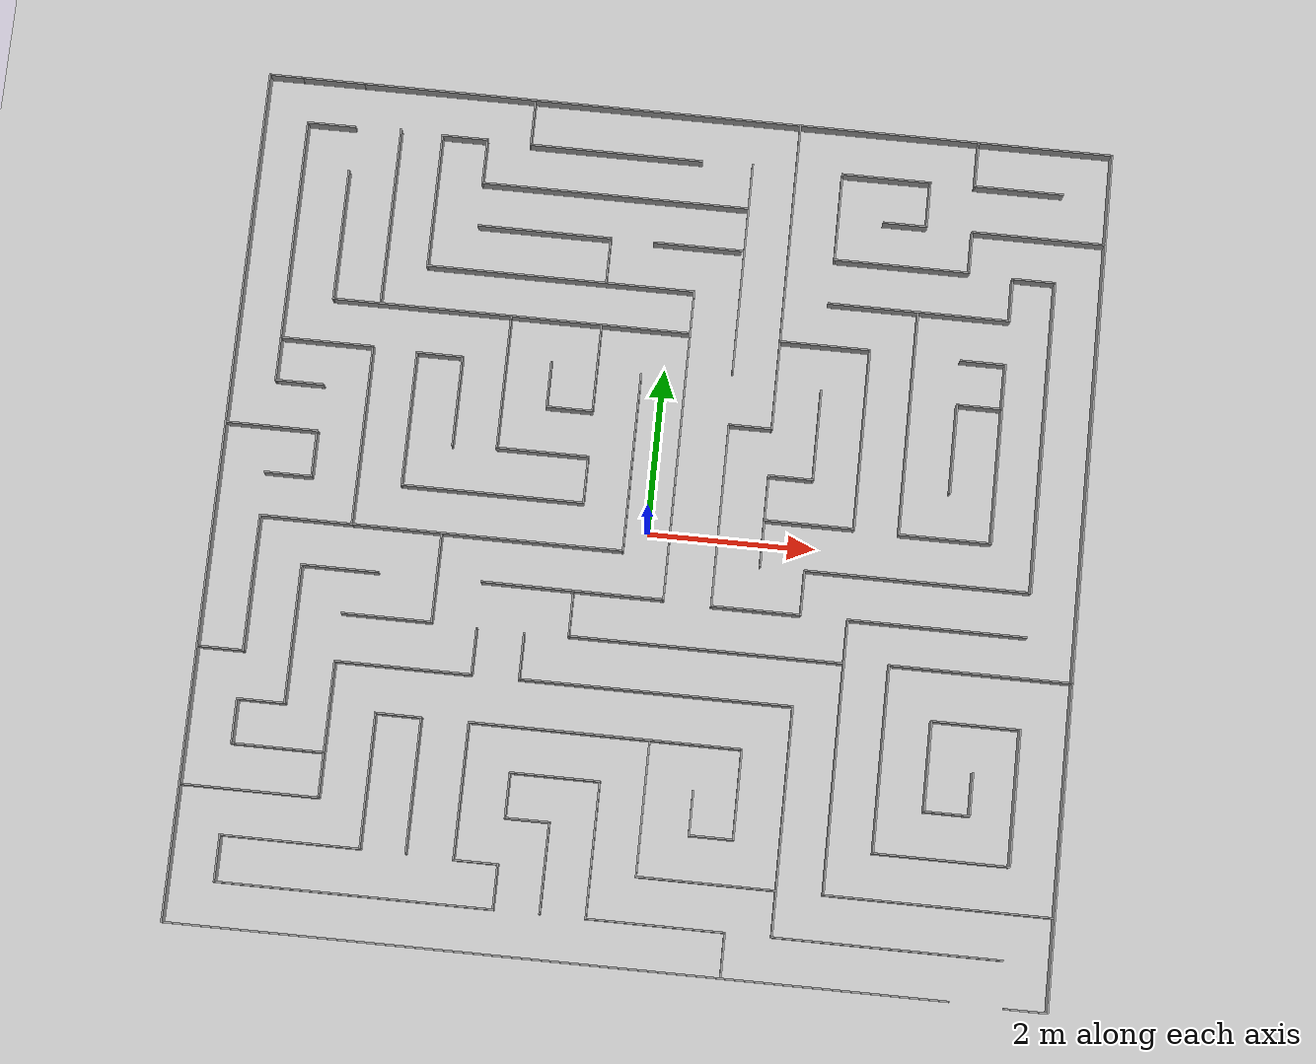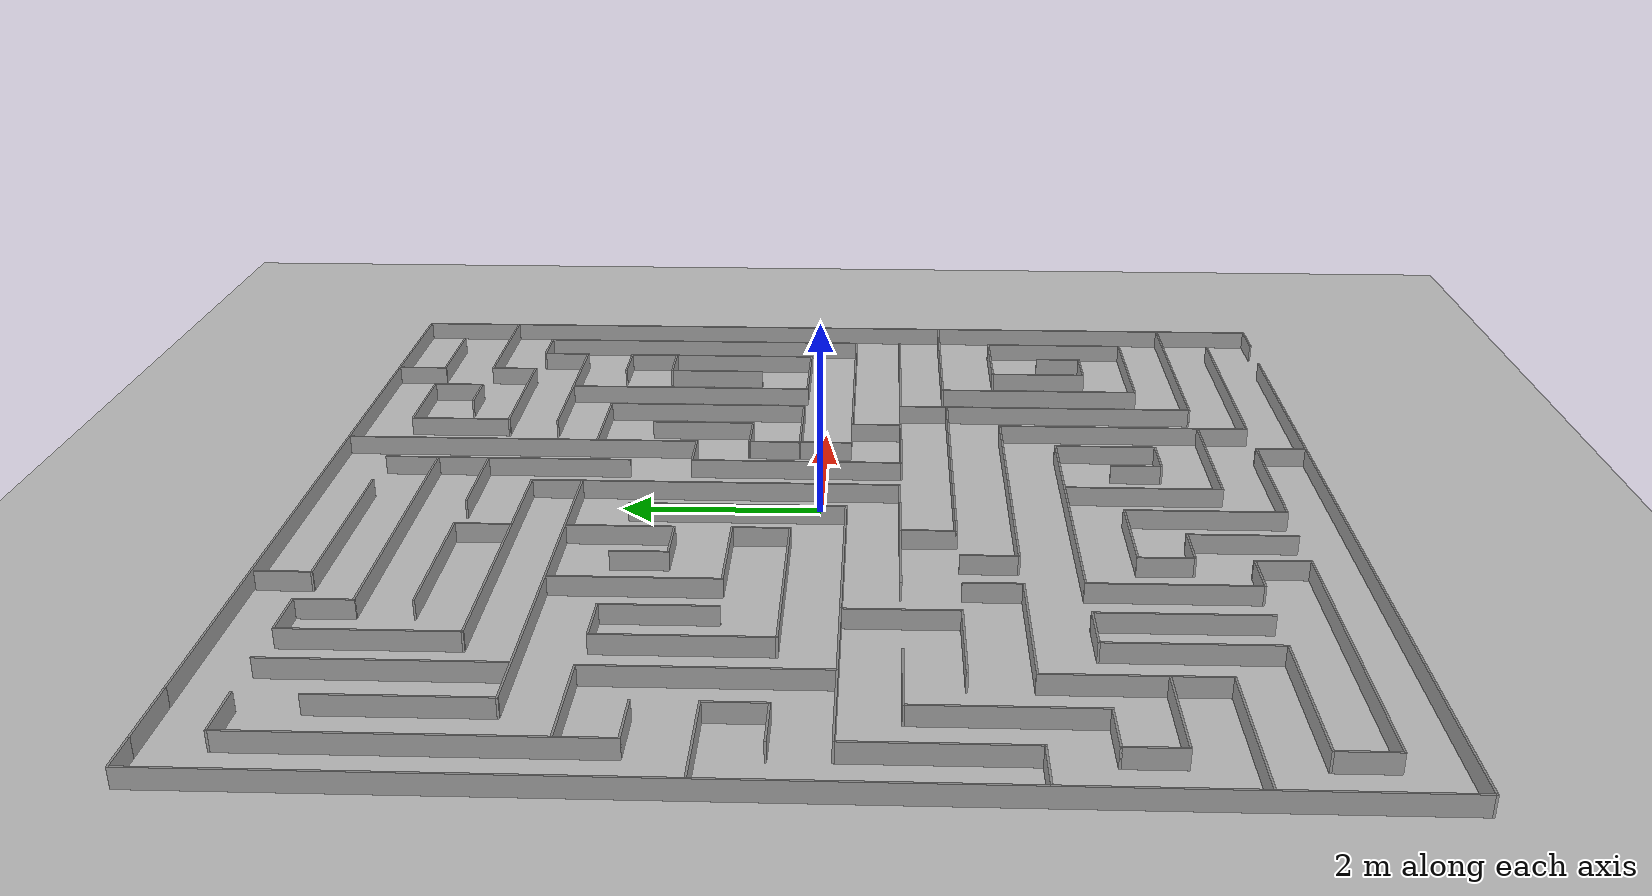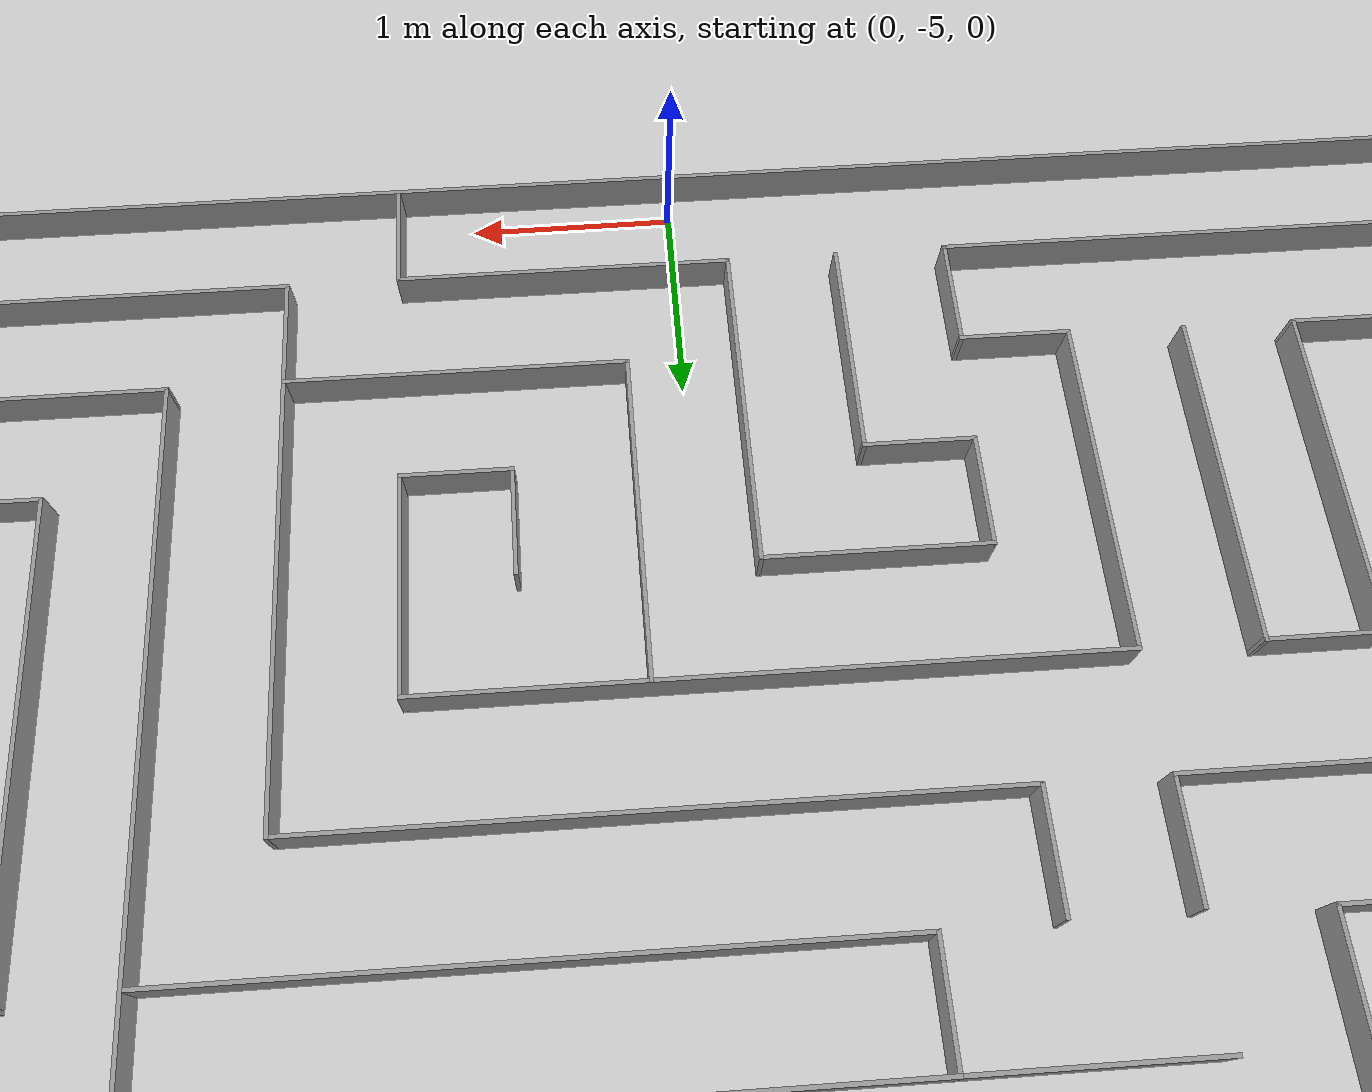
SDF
<sdf version="1.7">
 <world name="default">
  <light name="sun" type="directional">
   <pose>0 0 10 0 -0 0</pose>
   <diffuse>0.8 0.8 0.8 1</diffuse>
   <specular>0.2 0.2 0.2 1</specular>
   <attenuation>
    <range>1000</range>
    <constant>0.9</constant>
    <linear>0.01</linear>
    <quadratic>0.001</quadratic>
   </attenuation>
   <direction>-0.5 0.1 -0.9</direction>
   <spot><inner_angle>0</inner_angle><outer_angle>0</outer_angle><falloff>0</falloff></spot>
  </light>
  <model name="ground_plane">
   <static>1</static>
   <link name="link">
    <collision name="collision">
     <geometry><plane><normal>0 0 1</normal><size>100 100</size></plane></geometry>
     <surface><friction><ode><mu>100</mu><mu2>50</mu2></ode></friction></surface>
    </collision>
    <visual name="visual">
     <cast_shadows>0</cast_shadows>
     <geometry><plane><normal>0 0 1</normal><size>100 100</size></plane></geometry>
     <material>
      <script><uri>file://media/materials/scripts/gazebo.material</uri><name>Gazebo/Grey</name></script>
     </material>
    </visual>
   </link>
  </model>
  <gravity>0 0 -9.8</gravity>
  <magnetic_field>6e-06 2.3e-05 -4.2e-05</magnetic_field>
  <atmosphere type="adiabatic"/>
  <physics type="ode">
   <max_step_size>0.001</max_step_size>
   <real_time_factor>1</real_time_factor>
   <real_time_update_rate>1000</real_time_update_rate>
  </physics>
  <scene><ambient>0.4 0.4 0.4 1</ambient><background>0.7 0.7 0.7 1</background><shadows>1</shadows></scene>
  <audio><device>default</device></audio>
  <spherical_coordinates>
   <surface_model>EARTH_WGS84</surface_model>
   <latitude_deg>0</latitude_deg>
   <longitude_deg>0</longitude_deg>
   <elevation>0</elevation>
   <heading_deg>0</heading_deg>
  </spherical_coordinates>
  <model name="Maze_V3">
   <pose>-0.002 0.009 0 0 -0 0</pose>
   <link name="Wall_100">
    <collision name="Wall_100_Collision">
     <geometry><box><size>1.084 0.02 0.2</size></box></geometry>
     <pose>0 0 0.1 0 -0 0</pose>
    </collision>
    <visual name="Wall_100_Visual">
     <pose>0 0 0.1 0 -0 0</pose>
     <geometry><box><size>1.084 0.02 0.2</size></box></geometry>
     <material>
      <script><uri>file://media/materials/scripts/gazebo.material</uri><name>Gazebo/Grey</name></script>
      <ambient>1 1 1 1</ambient>
     </material>
     <meta><layer>0</layer></meta>
    </visual>
    <pose>-0.802 -4.088 0 0 -0 1.5708</pose>
   </link>
   <link name="Wall_102">
    <collision name="Wall_102_Collision">
     <geometry><box><size>0.54 0.02 0.2</size></box></geometry>
     <pose>0 0 0.1 0 -0 0</pose>
    </collision>
    <visual name="Wall_102_Visual">
     <pose>0 0 0.1 0 -0 0</pose>
     <geometry><box><size>0.54 0.02 0.2</size></box></geometry>
     <material>
      <script><uri>file://media/materials/scripts/gazebo.material</uri><name>Gazebo/Grey</name></script>
      <ambient>1 1 1 1</ambient>
     </material>
     <meta><layer>0</layer></meta>
    </visual>
    <pose>-1.062 -3.556 0 0 -0 3.14159</pose>
   </link>
   <link name="Wall_104">
    <collision name="Wall_104_Collision">
     <geometry><box><size>0.554 0.02 0.2</size></box></geometry>
     <pose>0 0 0.1 0 -0 0</pose>
    </collision>
    <visual name="Wall_104_Visual">
     <pose>0 0 0.1 0 -0 0</pose>
     <geometry><box><size>0.554 0.02 0.2</size></box></geometry>
     <material>
      <script><uri>file://media/materials/scripts/gazebo.material</uri><name>Gazebo/Grey</name></script>
      <ambient>1 1 1 1</ambient>
     </material>
     <meta><layer>0</layer></meta>
    </visual>
    <pose>-1.322 -3.289 0 0 -0 1.5708</pose>
   </link>
   <link name="Wall_106">
    <collision name="Wall_106_Collision">
     <geometry><box><size>1.079 0.02 0.2</size></box></geometry>
     <pose>0 0 0.1 0 -0 0</pose>
    </collision>
    <visual name="Wall_106_Visual">
     <pose>0 0 0.1 0 -0 0</pose>
     <geometry><box><size>1.079 0.02 0.2</size></box></geometry>
     <material>
      <script><uri>file://media/materials/scripts/gazebo.material</uri><name>Gazebo/Grey</name></script>
      <ambient>1 1 1 1</ambient>
     </material>
     <meta><layer>0</layer></meta>
    </visual>
    <pose>-0.7925 -3.022 0 0 -0 0</pose>
   </link>
   <link name="Wall_108">
    <collision name="Wall_108_Collision">
     <geometry><box><size>1.622 0.02 0.2</size></box></geometry>
     <pose>0 0 0.1 0 -0 0</pose>
    </collision>
    <visual name="Wall_108_Visual">
     <pose>0 0 0.1 0 -0 0</pose>
     <geometry><box><size>1.622 0.02 0.2</size></box></geometry>
     <material>
      <script><uri>file://media/materials/scripts/gazebo.material</uri><name>Gazebo/Grey</name></script>
      <ambient>1 1 1 1</ambient>
     </material>
     <meta><layer>0</layer></meta>
    </visual>
    <pose>-0.263 -3.823 0 0 -0 -1.5708</pose>
   </link>
   <link name="Wall_110">
    <collision name="Wall_110_Collision">
     <geometry><box><size>1.646 0.02 0.2</size></box></geometry>
     <pose>0 0 0.1 0 -0 0</pose>
    </collision>
    <visual name="Wall_110_Visual">
     <pose>0 0 0.1 0 -0 0</pose>
     <geometry><box><size>1.646 0.02 0.2</size></box></geometry>
     <material>
      <script><uri>file://media/materials/scripts/gazebo.material</uri><name>Gazebo/Grey</name></script>
      <ambient>1 1 1 1</ambient>
     </material>
     <meta><layer>0</layer></meta>
    </visual>
    <pose>0.55 -4.624 0 0 -0 0</pose>
   </link>
   <link name="Wall_112">
    <collision name="Wall_112_Collision">
     <geometry><box><size>0.54 0.02 0.2</size></box></geometry>
     <pose>0 0 0.1 0 -0 0</pose>
    </collision>
    <visual name="Wall_112_Visual">
     <pose>0 0 0.1 0 -0 0</pose>
     <geometry><box><size>0.54 0.02 0.2</size></box></geometry>
     <material>
      <script><uri>file://media/materials/scripts/gazebo.material</uri><name>Gazebo/Grey</name></script>
      <ambient>1 1 1 1</ambient>
     </material>
     <meta><layer>0</layer></meta>
    </visual>
    <pose>1.363 -4.884 0 0 -0 -1.5708</pose>
   </link>
   <link name="Wall_114">
    <collision name="Wall_114_Collision">
     <geometry><box><size>1.6199 0.02 0.2</size></box></geometry>
     <pose>0 0 0.1 0 -0 0</pose>
    </collision>
    <visual name="Wall_114_Visual">
     <pose>0 0 0.1 0 -0 0</pose>
     <geometry><box><size>1.6199 0.02 0.2</size></box></geometry>
     <material>
      <script><uri>file://media/materials/scripts/gazebo.material</uri><name>Gazebo/Grey</name></script>
      <ambient>1 1 1 1</ambient>
     </material>
     <meta><layer>0</layer></meta>
    </visual>
    <pose>0.271 -3.282 0 0 -0 -1.5708</pose>
   </link>
   <link name="Wall_116">
    <collision name="Wall_116_Collision">
     <geometry><box><size>1.659 0.02 0.2</size></box></geometry>
     <pose>0 0 0.1 0 -0 0</pose>
    </collision>
    <visual name="Wall_116_Visual">
     <pose>0 0 0.1 0 -0 0</pose>
     <geometry><box><size>1.659 0.02 0.2</size></box></geometry>
     <material>
      <script><uri>file://media/materials/scripts/gazebo.material</uri><name>Gazebo/Grey</name></script>
      <ambient>1 1 1 1</ambient>
     </material>
     <meta><layer>0</layer></meta>
    </visual>
    <pose>1.0905 -4.082 0 0 -0 0</pose>
   </link>
   <link name="Wall_118">
    <collision name="Wall_118_Collision">
     <geometry><box><size>0.559 0.02 0.2</size></box></geometry>
     <pose>0 0 0.1 0 -0 0</pose>
    </collision>
    <visual name="Wall_118_Visual">
     <pose>0 0 0.1 0 -0 0</pose>
     <geometry><box><size>0.559 0.02 0.2</size></box></geometry>
     <material>
      <script><uri>file://media/materials/scripts/gazebo.material</uri><name>Gazebo/Grey</name></script>
      <ambient>1 1 1 1</ambient>
     </material>
     <meta><layer>0</layer></meta>
    </visual>
    <pose>1.91 -4.3515 0 0 -0 -1.5708</pose>
   </link>
   <link name="Wall_120">
    <collision name="Wall_120_Collision">
     <geometry><box><size>2.714 0.02 0.2</size></box></geometry>
     <pose>0 0 0.1 0 -0 0</pose>
    </collision>
    <visual name="Wall_120_Visual">
     <pose>0 0 0.1 0 -0 0</pose>
     <geometry><box><size>2.714 0.02 0.2</size></box></geometry>
     <material>
      <script><uri>file://media/materials/scripts/gazebo.material</uri><name>Gazebo/Grey</name></script>
      <ambient>1 1 1 1</ambient>
     </material>
     <meta><layer>0</layer></meta>
    </visual>
    <pose>3.257 -4.621 0 0 -0 0</pose>
   </link>
   <link name="Wall_122">
    <collision name="Wall_122_Collision">
     <geometry><box><size>2.711 0.02 0.2</size></box></geometry>
     <pose>0 0 0.1 0 -0 0</pose>
    </collision>
    <visual name="Wall_122_Visual">
     <pose>0 0 0.1 0 -0 0</pose>
     <geometry><box><size>2.711 0.02 0.2</size></box></geometry>
     <material>
      <script><uri>file://media/materials/scripts/gazebo.material</uri><name>Gazebo/Grey</name></script>
      <ambient>1 1 1 1</ambient>
     </material>
     <meta><layer>0</layer></meta>
    </visual>
    <pose>3.8075 -4.077 0 0 -0 3.14159</pose>
   </link>
   <link name="Wall_124">
    <collision name="Wall_124_Collision">
     <geometry><box><size>3.26923 0.02 0.2</size></box></geometry>
     <pose>0 0 0.1 0 -0 0</pose>
    </collision>
    <visual name="Wall_124_Visual">
     <pose>0 0 0.1 0 -0 0</pose>
     <geometry><box><size>3.26923 0.02 0.2</size></box></geometry>
     <material>
      <script><uri>file://media/materials/scripts/gazebo.material</uri><name>Gazebo/Grey</name></script>
      <ambient>1 1 1 1</ambient>
     </material>
     <meta><layer>0</layer></meta>
    </visual>
    <pose>2.462 -2.4525 0 0 -0 1.5708</pose>
   </link>
   <link name="Wall_126">
    <collision name="Wall_126_Collision">
     <geometry><box><size>2.14234 0.02 0.2</size></box></geometry>
     <pose>0 0 0.1 0 -0 0</pose>
    </collision>
    <visual name="Wall_126_Visual">
     <pose>0 0 0.1 0 -0 0</pose>
     <geometry><box><size>2.14234 0.02 0.2</size></box></geometry>
     <material>
      <script><uri>file://media/materials/scripts/gazebo.material</uri><name>Gazebo/Grey</name></script>
      <ambient>1 1 1 1</ambient>
     </material>
     <meta><layer>0</layer></meta>
    </visual>
    <pose>3.52317 -0.82789 0 0 -0 0.000103</pose>
   </link>
   <link name="Wall_128">
    <collision name="Wall_128_Collision">
     <geometry><box><size>2.178 0.02 0.2</size></box></geometry>
     <pose>0 0 0.1 0 -0 0</pose>
    </collision>
    <visual name="Wall_128_Visual">
     <pose>0 0 0.1 0 -0 0</pose>
     <geometry><box><size>2.178 0.02 0.2</size></box></geometry>
     <material>
      <script><uri>file://media/materials/scripts/gazebo.material</uri><name>Gazebo/Grey</name></script>
      <ambient>1 1 1 1</ambient>
     </material>
     <meta><layer>0</layer></meta>
    </visual>
    <pose>4.076 -1.319 0 0 -0 3.14159</pose>
   </link>
   <link name="Wall_130">
    <collision name="Wall_130_Collision">
     <geometry><box><size>2.238 0.02 0.2</size></box></geometry>
     <pose>0 0 0.1 0 -0 0</pose>
    </collision>
    <visual name="Wall_130_Visual">
     <pose>0 0 0.1 0 -0 0</pose>
     <geometry><box><size>2.238 0.02 0.2</size></box></geometry>
     <material>
      <script><uri>file://media/materials/scripts/gazebo.material</uri><name>Gazebo/Grey</name></script>
      <ambient>1 1 1 1</ambient>
     </material>
     <meta><layer>0</layer></meta>
    </visual>
    <pose>2.997 -2.428 0 0 -0 -1.5708</pose>
   </link>
   <link name="Wall_132">
    <collision name="Wall_132_Collision">
     <geometry><box><size>1.62 0.02 0.2</size></box></geometry>
     <pose>0 0 0.1 0 -0 0</pose>
    </collision>
    <visual name="Wall_132_Visual">
     <pose>0 0 0.1 0 -0 0</pose>
     <geometry><box><size>1.62 0.02 0.2</size></box></geometry>
     <material>
      <script><uri>file://media/materials/scripts/gazebo.material</uri><name>Gazebo/Grey</name></script>
      <ambient>1 1 1 1</ambient>
     </material>
     <meta><layer>0</layer></meta>
    </visual>
    <pose>3.797 -3.537 0 0 -0 0</pose>
   </link>
   <link name="Wall_134">
    <collision name="Wall_134_Collision">
     <geometry><box><size>1.63 0.02 0.2</size></box></geometry>
     <pose>0 0 0.1 0 -0 0</pose>
    </collision>
    <visual name="Wall_134_Visual">
     <pose>0 0 0.1 0 -0 0</pose>
     <geometry><box><size>1.63 0.02 0.2</size></box></geometry>
     <material>
      <script><uri>file://media/materials/scripts/gazebo.material</uri><name>Gazebo/Grey</name></script>
      <ambient>1 1 1 1</ambient>
     </material>
     <meta><layer>0</layer></meta>
    </visual>
    <pose>4.597 -2.732 0 0 -0 1.5708</pose>
   </link>
   <link name="Wall_136">
    <collision name="Wall_136_Collision">
     <geometry><box><size>1.067 0.02 0.2</size></box></geometry>
     <pose>0 0 0.1 0 -0 0</pose>
    </collision>
    <visual name="Wall_136_Visual">
     <pose>0 0 0.1 0 -0 0</pose>
     <geometry><box><size>1.067 0.02 0.2</size></box></geometry>
     <material>
      <script><uri>file://media/materials/scripts/gazebo.material</uri><name>Gazebo/Grey</name></script>
      <ambient>1 1 1 1</ambient>
     </material>
     <meta><layer>0</layer></meta>
    </visual>
    <pose>4.0735 -1.927 0 0 -0 3.14159</pose>
   </link>
   <link name="Wall_138">
    <collision name="Wall_138_Collision">
     <geometry><box><size>1.086 0.02 0.2</size></box></geometry>
     <pose>0 0 0.1 0 -0 0</pose>
    </collision>
    <visual name="Wall_138_Visual">
     <pose>0 0 0.1 0 -0 0</pose>
     <geometry><box><size>1.086 0.02 0.2</size></box></geometry>
     <material>
      <script><uri>file://media/materials/scripts/gazebo.material</uri><name>Gazebo/Grey</name></script>
      <ambient>1 1 1 1</ambient>
     </material>
     <meta><layer>0</layer></meta>
    </visual>
    <pose>3.55 -2.46 0 0 -0 -1.5708</pose>
   </link>
   <link name="Wall_140">
    <collision name="Wall_140_Collision">
     <geometry><box><size>0.553 0.02 0.2</size></box></geometry>
     <pose>0 0 0.1 0 -0 0</pose>
    </collision>
    <visual name="Wall_140_Visual">
     <pose>0 0 0.1 0 -0 0</pose>
     <geometry><box><size>0.553 0.02 0.2</size></box></geometry>
     <material>
      <script><uri>file://media/materials/scripts/gazebo.material</uri><name>Gazebo/Grey</name></script>
      <ambient>1 1 1 1</ambient>
     </material>
     <meta><layer>0</layer></meta>
    </visual>
    <pose>3.8165 -2.993 0 0 -0 0</pose>
   </link>
   <link name="Wall_142">
    <collision name="Wall_142_Collision">
     <geometry><box><size>0.52 0.02 0.2</size></box></geometry>
     <pose>0 0 0.1 0 -0 0</pose>
    </collision>
    <visual name="Wall_142_Visual">
     <pose>0 0 0.1 0 -0 0</pose>
     <geometry><box><size>0.52 0.02 0.2</size></box></geometry>
     <material>
      <script><uri>file://media/materials/scripts/gazebo.material</uri><name>Gazebo/Grey</name></script>
      <ambient>1 1 1 1</ambient>
     </material>
     <meta><layer>0</layer></meta>
    </visual>
    <pose>4.083 -2.743 0 0 -0 1.5708</pose>
   </link>
   <link name="Wall_144">
    <collision name="Wall_144_Collision">
     <geometry><box><size>2.185 0.02 0.2</size></box></geometry>
     <pose>0 0 0.1 0 -0 0</pose>
    </collision>
    <visual name="Wall_144_Visual">
     <pose>0 0 0.1 0 -0 0</pose>
     <geometry><box><size>2.185 0.02 0.2</size></box></geometry>
     <material>
      <script><uri>file://media/materials/scripts/gazebo.material</uri><name>Gazebo/Grey</name></script>
      <ambient>1 1 1 1</ambient>
     </material>
     <meta><layer>0</layer></meta>
    </visual>
    <pose>1.91 -2.9995 0 0 -0 1.5708</pose>
   </link>
   <link name="Wall_146">
    <collision name="Wall_146_Collision">
     <geometry><box><size>3.263 0.02 0.2</size></box></geometry>
     <pose>0 0 0.1 0 -0 0</pose>
    </collision>
    <visual name="Wall_146_Visual">
     <pose>0 0 0.1 0 -0 0</pose>
     <geometry><box><size>3.263 0.02 0.2</size></box></geometry>
     <material>
      <script><uri>file://media/materials/scripts/gazebo.material</uri><name>Gazebo/Grey</name></script>
      <ambient>1 1 1 1</ambient>
     </material>
     <meta><layer>0</layer></meta>
    </visual>
    <pose>0.2885 -1.917 0 0 -0 3.14159</pose>
   </link>
   <link name="Wall_148">
    <collision name="Wall_148_Collision">
     <geometry><box><size>0.57 0.02 0.2</size></box></geometry>
     <pose>0 0 0.1 0 -0 0</pose>
    </collision>
    <visual name="Wall_148_Visual">
     <pose>0 0 0.1 0 -0 0</pose>
     <geometry><box><size>0.57 0.02 0.2</size></box></geometry>
     <material>
      <script><uri>file://media/materials/scripts/gazebo.material</uri><name>Gazebo/Grey</name></script>
      <ambient>1 1 1 1</ambient>
     </material>
     <meta><layer>0</layer></meta>
    </visual>
    <pose>-1.333 -1.642 0 0 -0 1.5708</pose>
   </link>
   <link name="Wall_150">
    <collision name="Wall_150_Collision">
     <geometry><box><size>1.106 0.02 0.2</size></box></geometry>
     <pose>0 0 0.1 0 -0 0</pose>
    </collision>
    <visual name="Wall_150_Visual">
     <pose>0 0 0.1 0 -0 0</pose>
     <geometry><box><size>1.106 0.02 0.2</size></box></geometry>
     <material>
      <script><uri>file://media/materials/scripts/gazebo.material</uri><name>Gazebo/Grey</name></script>
      <ambient>1 1 1 1</ambient>
     </material>
     <meta><layer>0</layer></meta>
    </visual>
    <pose>-3.522 -2.463 0 0 -0 1.5708</pose>
   </link>
   <link name="Wall_152">
    <collision name="Wall_152_Collision">
     <geometry><box><size>1.644 0.02 0.2</size></box></geometry>
     <pose>0 0 0.1 0 -0 0</pose>
    </collision>
    <visual name="Wall_152_Visual">
     <pose>0 0 0.1 0 -0 0</pose>
     <geometry><box><size>1.644 0.02 0.2</size></box></geometry>
     <material>
      <script><uri>file://media/materials/scripts/gazebo.material</uri><name>Gazebo/Grey</name></script>
      <ambient>1 1 1 1</ambient>
     </material>
     <meta><layer>0</layer></meta>
    </visual>
    <pose>-2.71 -1.92 0 0 -0 0</pose>
   </link>
   <link name="Wall_154">
    <collision name="Wall_154_Collision">
     <geometry><box><size>0.57 0.02 0.2</size></box></geometry>
     <pose>0 0 0.1 0 -0 0</pose>
    </collision>
    <visual name="Wall_154_Visual">
     <pose>0 0 0.1 0 -0 0</pose>
     <geometry><box><size>0.57 0.02 0.2</size></box></geometry>
     <material>
      <script><uri>file://media/materials/scripts/gazebo.material</uri><name>Gazebo/Grey</name></script>
      <ambient>1 1 1 1</ambient>
     </material>
     <meta><layer>0</layer></meta>
    </visual>
    <pose>-1.898 -1.645 0 0 -0 1.5708</pose>
   </link>
   <link name="Wall_156">
    <collision name="Wall_156_Collision">
     <geometry><box><size>1.088 0.02 0.2</size></box></geometry>
     <pose>0 0 0.1 0 -0 0</pose>
    </collision>
    <visual name="Wall_156_Visual">
     <pose>0 0 0.1 0 -0 0</pose>
     <geometry><box><size>1.088 0.02 0.2</size></box></geometry>
     <material>
      <script><uri>file://media/materials/scripts/gazebo.material</uri><name>Gazebo/Grey</name></script>
      <ambient>1 1 1 1</ambient>
     </material>
     <meta><layer>0</layer></meta>
    </visual>
    <pose>-2.971 -1.344 0 0 -0 0</pose>
   </link>
   <link name="Wall_158">
    <collision name="Wall_158_Collision">
     <geometry><box><size>1.093 0.02 0.2</size></box></geometry>
     <pose>0 0 0.1 0 -0 0</pose>
    </collision>
    <visual name="Wall_158_Visual">
     <pose>0 0 0.1 0 -0 0</pose>
     <geometry><box><size>1.093 0.02 0.2</size></box></geometry>
     <material>
      <script><uri>file://media/materials/scripts/gazebo.material</uri><name>Gazebo/Grey</name></script>
      <ambient>1 1 1 1</ambient>
     </material>
     <meta><layer>0</layer></meta>
    </visual>
    <pose>-2.437 -0.8075 0 0 -0 1.5708</pose>
   </link>
   <link name="Wall_16">
    <collision name="Wall_16_Collision">
     <geometry><box><size>9.2 0.02 0.2</size></box></geometry>
     <pose>0 0 0.1 0 -0 0</pose>
    </collision>
    <visual name="Wall_16_Visual">
     <pose>0 0 0.1 0 -0 0</pose>
     <geometry><box><size>9.2 0.02 0.2</size></box></geometry>
     <material>
      <script><uri>file://media/materials/scripts/gazebo.material</uri><name>Gazebo/Grey</name></script>
      <ambient>1 1 1 1</ambient>
     </material>
     <meta><layer>0</layer></meta>
    </visual>
    <pose>-0.573 -5.151 0 0 -0 3.14159</pose>
   </link>
   <link name="Wall_161">
    <collision name="Wall_161_Collision">
     <geometry><box><size>1.097 0.02 0.2</size></box></geometry>
     <pose>0 0 0.1 0 -0 0</pose>
    </collision>
    <visual name="Wall_161_Visual">
     <pose>0 0 0.1 0 -0 0</pose>
     <geometry><box><size>1.097 0.02 0.2</size></box></geometry>
     <material>
      <script><uri>file://media/materials/scripts/gazebo.material</uri><name>Gazebo/Grey</name></script>
      <ambient>1 1 1 1</ambient>
     </material>
     <meta><layer>0</layer></meta>
    </visual>
    <pose>-2.9755 -0.271 0 0 -0 3.14159</pose>
   </link>
   <link name="Wall_163">
    <collision name="Wall_163_Collision">
     <geometry><box><size>2.186 0.02 0.2</size></box></geometry>
     <pose>0 0 0.1 0 -0 0</pose>
    </collision>
    <visual name="Wall_163_Visual">
     <pose>0 0 0.1 0 -0 0</pose>
     <geometry><box><size>2.186 0.02 0.2</size></box></geometry>
     <material>
      <script><uri>file://media/materials/scripts/gazebo.material</uri><name>Gazebo/Grey</name></script>
      <ambient>1 1 1 1</ambient>
     </material>
     <meta><layer>0</layer></meta>
    </visual>
    <pose>-1.354 -0.271 0 0 -0 0</pose>
   </link>
   <link name="Wall_165">
    <collision name="Wall_165_Collision">
     <geometry><box><size>1.113 0.02 0.2</size></box></geometry>
     <pose>0 0 0.1 0 -0 0</pose>
    </collision>
    <visual name="Wall_165_Visual">
     <pose>0 0 0.1 0 -0 0</pose>
     <geometry><box><size>1.113 0.02 0.2</size></box></geometry>
     <material>
      <script><uri>file://media/materials/scripts/gazebo.material</uri><name>Gazebo/Grey</name></script>
      <ambient>1 1 1 1</ambient>
     </material>
     <meta><layer>0</layer></meta>
    </visual>
    <pose>-1.3515 -0.806 0 0 -0 0</pose>
   </link>
   <link name="Wall_167">
    <collision name="Wall_167_Collision">
     <geometry><box><size>0.564 0.02 0.2</size></box></geometry>
     <pose>0 0 0.1 0 -0 0</pose>
    </collision>
    <visual name="Wall_167_Visual">
     <pose>0 0 0.1 0 -0 0</pose>
     <geometry><box><size>0.564 0.02 0.2</size></box></geometry>
     <material>
      <script><uri>file://media/materials/scripts/gazebo.material</uri><name>Gazebo/Grey</name></script>
      <ambient>1 1 1 1</ambient>
     </material>
     <meta><layer>0</layer></meta>
    </visual>
    <pose>-0.805 -1.078 0 0 -0 -1.5708</pose>
   </link>
   <link name="Wall_169">
    <collision name="Wall_169_Collision">
     <geometry><box><size>3.269 0.02 0.2</size></box></geometry>
     <pose>0 0 0.1 0 -0 0</pose>
    </collision>
    <visual name="Wall_169_Visual">
     <pose>0 0 0.1 0 -0 0</pose>
     <geometry><box><size>3.269 0.02 0.2</size></box></geometry>
     <material>
      <script><uri>file://media/materials/scripts/gazebo.material</uri><name>Gazebo/Grey</name></script>
      <ambient>1 1 1 1</ambient>
     </material>
     <meta><layer>0</layer></meta>
    </visual>
    <pose>0.8195 -1.35 0 0 -0 0</pose>
   </link>
   <link name="Wall_171">
    <collision name="Wall_171_Collision">
     <geometry><box><size>1.091 0.02 0.2</size></box></geometry>
     <pose>0 0 0.1 0 -0 0</pose>
    </collision>
    <visual name="Wall_171_Visual">
     <pose>0 0 0.1 0 -0 0</pose>
     <geometry><box><size>1.091 0.02 0.2</size></box></geometry>
     <material>
      <script><uri>file://media/materials/scripts/gazebo.material</uri><name>Gazebo/Grey</name></script>
      <ambient>1 1 1 1</ambient>
     </material>
     <meta><layer>0</layer></meta>
    </visual>
    <pose>-0.2695 -0.806 0 0 -0 0</pose>
   </link>
   <link name="Wall_173">
    <collision name="Wall_173_Collision">
     <geometry><box><size>3.795 0.02 0.2</size></box></geometry>
     <pose>0 0 0.1 0 -0 0</pose>
    </collision>
    <visual name="Wall_173_Visual">
     <pose>0 0 0.1 0 -0 0</pose>
     <geometry><box><size>3.795 0.02 0.2</size></box></geometry>
     <material>
      <script><uri>file://media/materials/scripts/gazebo.material</uri><name>Gazebo/Grey</name></script>
      <ambient>1 1 1 1</ambient>
     </material>
     <meta><layer>0</layer></meta>
    </visual>
    <pose>0.266 1.0815 0 0 -0 1.5708</pose>
   </link>
   <link name="Wall_175">
    <collision name="Wall_175_Collision">
     <geometry><box><size>1.083 0.02 0.2</size></box></geometry>
     <pose>0 0 0.1 0 -0 0</pose>
    </collision>
    <visual name="Wall_175_Visual">
     <pose>0 0 0.1 0 -0 0</pose>
     <geometry><box><size>1.083 0.02 0.2</size></box></geometry>
     <material>
      <script><uri>file://media/materials/scripts/gazebo.material</uri><name>Gazebo/Grey</name></script>
      <ambient>1 1 1 1</ambient>
     </material>
     <meta><layer>0</layer></meta>
    </visual>
    <pose>1.3705 -0.826 0 0 -0 0</pose>
   </link>
   <link name="Wall_177">
    <collision name="Wall_177_Collision">
     <geometry><box><size>0.554 0.02 0.2</size></box></geometry>
     <pose>0 0 0.1 0 -0 0</pose>
    </collision>
    <visual name="Wall_177_Visual">
     <pose>0 0 0.1 0 -0 0</pose>
     <geometry><box><size>0.554 0.02 0.2</size></box></geometry>
     <material>
      <script><uri>file://media/materials/scripts/gazebo.material</uri><name>Gazebo/Grey</name></script>
      <ambient>1 1 1 1</ambient>
     </material>
     <meta><layer>0</layer></meta>
    </visual>
    <pose>1.902 -0.559 0 0 -0 1.5708</pose>
   </link>
   <link name="Wall_179">
    <collision name="Wall_179_Collision">
     <geometry><box><size>2.714 0.02 0.2</size></box></geometry>
     <pose>0 0 0.1 0 -0 0</pose>
    </collision>
    <visual name="Wall_179_Visual">
     <pose>0 0 0.1 0 -0 0</pose>
     <geometry><box><size>2.714 0.02 0.2</size></box></geometry>
     <material>
      <script><uri>file://media/materials/scripts/gazebo.material</uri><name>Gazebo/Grey</name></script>
      <ambient>1 1 1 1</ambient>
     </material>
     <meta><layer>0</layer></meta>
    </visual>
    <pose>3.249 -0.292 0 0 -0 0</pose>
   </link>
   <link name="Wall_18">
    <collision name="Wall_18_Collision">
     <geometry><box><size>10.341 0.02 0.2</size></box></geometry>
     <pose>0 0 0.1 0 -0 0</pose>
    </collision>
    <visual name="Wall_18_Visual">
     <pose>0 0 0.1 0 -0 0</pose>
     <geometry><box><size>10.341 0.02 0.2</size></box></geometry>
     <material>
      <script><uri>file://media/materials/scripts/gazebo.material</uri><name>Gazebo/Grey</name></script>
      <ambient>1 1 1 1</ambient>
     </material>
     <meta><layer>0</layer></meta>
    </visual>
    <pose>-5.163 0.0095 0 0 -0 1.5708</pose>
   </link>
   <link name="Wall_182">
    <collision name="Wall_182_Collision">
     <geometry><box><size>3.82 0.02 0.2</size></box></geometry>
     <pose>0 0 0.1 0 -0 0</pose>
    </collision>
    <visual name="Wall_182_Visual">
     <pose>0 0 0.1 0 -0 0</pose>
     <geometry><box><size>3.82 0.02 0.2</size></box></geometry>
     <material>
      <script><uri>file://media/materials/scripts/gazebo.material</uri><name>Gazebo/Grey</name></script>
      <ambient>1 1 1 1</ambient>
     </material>
     <meta><layer>0</layer></meta>
    </visual>
    <pose>4.596 1.608 0 0 -0 1.5708</pose>
   </link>
   <link name="Wall_184">
    <collision name="Wall_184_Collision">
     <geometry><box><size>0.532 0.02 0.2</size></box></geometry>
     <pose>0 0 0.1 0 -0 0</pose>
    </collision>
    <visual name="Wall_184_Visual">
     <pose>0 0 0.1 0 -0 0</pose>
     <geometry><box><size>0.532 0.02 0.2</size></box></geometry>
     <material>
      <script><uri>file://media/materials/scripts/gazebo.material</uri><name>Gazebo/Grey</name></script>
      <ambient>1 1 1 1</ambient>
     </material>
     <meta><layer>0</layer></meta>
    </visual>
    <pose>4.34 3.508 0 0 -0 3.14159</pose>
   </link>
   <link name="Wall_186">
    <collision name="Wall_186_Collision">
     <geometry><box><size>0.544 0.02 0.2</size></box></geometry>
     <pose>0 0 0.1 0 -0 0</pose>
    </collision>
    <visual name="Wall_186_Visual">
     <pose>0 0 0.1 0 -0 0</pose>
     <geometry><box><size>0.544 0.02 0.2</size></box></geometry>
     <material>
      <script><uri>file://media/materials/scripts/gazebo.material</uri><name>Gazebo/Grey</name></script>
      <ambient>1 1 1 1</ambient>
     </material>
     <meta><layer>0</layer></meta>
    </visual>
    <pose>4.084 3.246 0 0 -0 -1.5708</pose>
   </link>
   <link name="Wall_188">
    <collision name="Wall_188_Collision">
     <geometry><box><size>2.209 0.02 0.2</size></box></geometry>
     <pose>0 0 0.1 0 -0 0</pose>
    </collision>
    <visual name="Wall_188_Visual">
     <pose>0 0 0.1 0 -0 0</pose>
     <geometry><box><size>2.209 0.02 0.2</size></box></geometry>
     <material>
      <script><uri>file://media/materials/scripts/gazebo.material</uri><name>Gazebo/Grey</name></script>
      <ambient>1 1 1 1</ambient>
     </material>
     <meta><layer>0</layer></meta>
    </visual>
    <pose>2.9895 2.984 0 0 -0 3.14159</pose>
   </link>
   <link name="Wall_190">
    <collision name="Wall_190_Collision">
     <geometry><box><size>2.738 0.02 0.2</size></box></geometry>
     <pose>0 0 0.1 0 -0 0</pose>
    </collision>
    <visual name="Wall_190_Visual">
     <pose>0 0 0.1 0 -0 0</pose>
     <geometry><box><size>2.738 0.02 0.2</size></box></geometry>
     <material>
      <script><uri>file://media/materials/scripts/gazebo.material</uri><name>Gazebo/Grey</name></script>
      <ambient>1 1 1 1</ambient>
     </material>
     <meta><layer>0</layer></meta>
    </visual>
    <pose>2.979 1.61 0 0 -0 -1.5708</pose>
   </link>
   <link name="Wall_192">
    <collision name="Wall_192_Collision">
     <geometry><box><size>1.12 0.02 0.2</size></box></geometry>
     <pose>0 0 0.1 0 -0 0</pose>
    </collision>
    <visual name="Wall_192_Visual">
     <pose>0 0 0.1 0 -0 0</pose>
     <geometry><box><size>1.12 0.02 0.2</size></box></geometry>
     <material>
      <script><uri>file://media/materials/scripts/gazebo.material</uri><name>Gazebo/Grey</name></script>
      <ambient>1 1 1 1</ambient>
     </material>
     <meta><layer>0</layer></meta>
    </visual>
    <pose>3.529 0.251 0 0 -0 0</pose>
   </link>
   <link name="Wall_194">
    <collision name="Wall_194_Collision">
     <geometry><box><size>2.208 0.02 0.2</size></box></geometry>
     <pose>0 0 0.1 0 -0 0</pose>
    </collision>
    <visual name="Wall_194_Visual">
     <pose>0 0 0.1 0 -0 0</pose>
     <geometry><box><size>2.208 0.02 0.2</size></box></geometry>
     <material>
      <script><uri>file://media/materials/scripts/gazebo.material</uri><name>Gazebo/Grey</name></script>
      <ambient>1 1 1 1</ambient>
     </material>
     <meta><layer>0</layer></meta>
    </visual>
    <pose>4.079 1.345 0 0 -0 1.5708</pose>
   </link>
   <link name="Wall_196">
    <collision name="Wall_196_Collision">
     <geometry><box><size>0.557 0.02 0.2</size></box></geometry>
     <pose>0 0 0.1 0 -0 0</pose>
    </collision>
    <visual name="Wall_196_Visual">
     <pose>0 0 0.1 0 -0 0</pose>
     <geometry><box><size>0.557 0.02 0.2</size></box></geometry>
     <material>
      <script><uri>file://media/materials/scripts/gazebo.material</uri><name>Gazebo/Grey</name></script>
      <ambient>1 1 1 1</ambient>
     </material>
     <meta><layer>0</layer></meta>
    </visual>
    <pose>3.8105 2.439 0 0 -0 3.14159</pose>
   </link>
   <link name="Wall_198">
    <collision name="Wall_198_Collision">
     <geometry><box><size>0.546 0.02 0.2</size></box></geometry>
     <pose>0 0 0.1 0 -0 0</pose>
    </collision>
    <visual name="Wall_198_Visual">
     <pose>0 0 0.1 0 -0 0</pose>
     <geometry><box><size>0.546 0.02 0.2</size></box></geometry>
     <material>
      <script><uri>file://media/materials/scripts/gazebo.material</uri><name>Gazebo/Grey</name></script>
      <ambient>1 1 1 1</ambient>
     </material>
     <meta><layer>0</layer></meta>
    </visual>
    <pose>3.805 1.892 0 0 -0 3.14159</pose>
   </link>
   <link name="Wall_20">
    <collision name="Wall_20_Collision">
     <geometry><box><size>0.42 0.02 0.2</size></box></geometry>
     <pose>0 0 0.1 0 -0 0</pose>
    </collision>
    <visual name="Wall_20_Visual">
     <pose>0 0 0.1 0 -0 0</pose>
     <geometry><box><size>0.42 0.02 0.2</size></box></geometry>
     <material>
      <script><uri>file://media/materials/scripts/gazebo.material</uri><name>Gazebo/Grey</name></script>
      <ambient>1 1 1 1</ambient>
     </material>
     <meta><layer>0</layer></meta>
    </visual>
    <pose>-4.963 5.17 0 0 -0 0</pose>
   </link>
   <link name="Wall_201">
    <collision name="Wall_201_Collision">
     <geometry><box><size>1.092 0.02 0.2</size></box></geometry>
     <pose>0 0 0.1 0 -0 0</pose>
    </collision>
    <visual name="Wall_201_Visual">
     <pose>0 0 0.1 0 -0 0</pose>
     <geometry><box><size>1.092 0.02 0.2</size></box></geometry>
     <material>
      <script><uri>file://media/materials/scripts/gazebo.material</uri><name>Gazebo/Grey</name></script>
      <ambient>1 1 1 1</ambient>
     </material>
     <meta><layer>0</layer></meta>
    </visual>
    <pose>3.542 1.356 0 0 -0 -1.5708</pose>
   </link>
   <link name="Wall_203">
    <collision name="Wall_203_Collision">
     <geometry><box><size>2.224 0.02 0.2</size></box></geometry>
     <pose>0 0 0.1 0 -0 0</pose>
    </collision>
    <visual name="Wall_203_Visual">
     <pose>0 0 0.1 0 -0 0</pose>
     <geometry><box><size>2.224 0.02 0.2</size></box></geometry>
     <material>
      <script><uri>file://media/materials/scripts/gazebo.material</uri><name>Gazebo/Grey</name></script>
      <ambient>1 1 1 1</ambient>
     </material>
     <meta><layer>0</layer></meta>
    </visual>
    <pose>0.839 0.276 0 0 -0 1.5708</pose>
   </link>
   <link name="Wall_205">
    <collision name="Wall_205_Collision">
     <geometry><box><size>0.537 0.02 0.2</size></box></geometry>
     <pose>0 0 0.1 0 -0 0</pose>
    </collision>
    <visual name="Wall_205_Visual">
     <pose>0 0 0.1 0 -0 0</pose>
     <geometry><box><size>0.537 0.02 0.2</size></box></geometry>
     <material>
      <script><uri>file://media/materials/scripts/gazebo.material</uri><name>Gazebo/Grey</name></script>
      <ambient>1 1 1 1</ambient>
     </material>
     <meta><layer>0</layer></meta>
    </visual>
    <pose>1.0975 1.378 0 0 -0 0</pose>
   </link>
   <link name="Wall_207">
    <collision name="Wall_207_Collision">
     <geometry><box><size>3.81 0.02 0.2</size></box></geometry>
     <pose>0 0 0.1 0 -0 0</pose>
    </collision>
    <visual name="Wall_207_Visual">
     <pose>0 0 0.1 0 -0 0</pose>
     <geometry><box><size>3.81 0.02 0.2</size></box></geometry>
     <material>
      <script><uri>file://media/materials/scripts/gazebo.material</uri><name>Gazebo/Grey</name></script>
      <ambient>1 1 1 1</ambient>
     </material>
     <meta><layer>0</layer></meta>
    </visual>
    <pose>1.356 3.273 0 0 -0 1.5708</pose>
   </link>
   <link name="Wall_209">
    <collision name="Wall_209_Collision">
     <geometry><box><size>0.552 0.02 0.2</size></box></geometry>
     <pose>0 0 0.1 0 -0 0</pose>
    </collision>
    <visual name="Wall_209_Visual">
     <pose>0 0 0.1 0 -0 0</pose>
     <geometry><box><size>0.552 0.02 0.2</size></box></geometry>
     <material>
      <script><uri>file://media/materials/scripts/gazebo.material</uri><name>Gazebo/Grey</name></script>
      <ambient>1 1 1 1</ambient>
     </material>
     <meta><layer>0</layer></meta>
    </visual>
    <pose>3.535 4.885 0 0 -0 -1.5708</pose>
   </link>
   <link name="Wall_211">
    <collision name="Wall_211_Collision">
     <geometry><box><size>1.092 0.02 0.2</size></box></geometry>
     <pose>0 0 0.1 0 -0 0</pose>
    </collision>
    <visual name="Wall_211_Visual">
     <pose>0 0 0.1 0 -0 0</pose>
     <geometry><box><size>1.092 0.02 0.2</size></box></geometry>
     <material>
      <script><uri>file://media/materials/scripts/gazebo.material</uri><name>Gazebo/Grey</name></script>
      <ambient>1 1 1 1</ambient>
     </material>
     <meta><layer>0</layer></meta>
    </visual>
    <pose>4.071 4.619 0 0 -0 0</pose>
   </link>
   <link name="Wall_213">
    <collision name="Wall_213_Collision">
     <geometry><box><size>1.61996 0.02 0.2</size></box></geometry>
     <pose>0 0 0.1 0 -0 0</pose>
    </collision>
    <visual name="Wall_213_Visual">
     <pose>0 0 0.1 0 -0 0</pose>
     <geometry><box><size>1.61996 0.02 0.2</size></box></geometry>
     <material>
      <script><uri>file://media/materials/scripts/gazebo.material</uri><name>Gazebo/Grey</name></script>
      <ambient>1 1 1 1</ambient>
     </material>
     <meta><layer>0</layer></meta>
    </visual>
    <pose>4.35 4.043 0 0 -0 3.14159</pose>
   </link>
   <link name="Wall_215">
    <collision name="Wall_215_Collision">
     <geometry><box><size>0.531 0.02 0.2</size></box></geometry>
     <pose>0 0 0.1 0 -0 0</pose>
    </collision>
    <visual name="Wall_215_Visual">
     <pose>0 0 0.1 0 -0 0</pose>
     <geometry><box><size>0.531 0.02 0.2</size></box></geometry>
     <material>
      <script><uri>file://media/materials/scripts/gazebo.material</uri><name>Gazebo/Grey</name></script>
      <ambient>1 1 1 1</ambient>
     </material>
     <meta><layer>0</layer></meta>
    </visual>
    <pose>3.55 3.7875 0 0 -0 -1.5708</pose>
   </link>
   <link name="Wall_217">
    <collision name="Wall_217_Collision">
     <geometry><box><size>1.651 0.02 0.2</size></box></geometry>
     <pose>0 0 0.1 0 -0 0</pose>
    </collision>
    <visual name="Wall_217_Visual">
     <pose>0 0 0.1 0 -0 0</pose>
     <geometry><box><size>1.651 0.02 0.2</size></box></geometry>
     <material>
      <script><uri>file://media/materials/scripts/gazebo.material</uri><name>Gazebo/Grey</name></script>
      <ambient>1 1 1 1</ambient>
     </material>
     <meta><layer>0</layer></meta>
    </visual>
    <pose>2.7345 3.532 0 0 -0 3.14159</pose>
   </link>
   <link name="Wall_219">
    <collision name="Wall_219_Collision">
     <geometry><box><size>1.098 0.02 0.2</size></box></geometry>
     <pose>0 0 0.1 0 -0 0</pose>
    </collision>
    <visual name="Wall_219_Visual">
     <pose>0 0 0.1 0 -0 0</pose>
     <geometry><box><size>1.098 0.02 0.2</size></box></geometry>
     <material>
      <script><uri>file://media/materials/scripts/gazebo.material</uri><name>Gazebo/Grey</name></script>
      <ambient>1 1 1 1</ambient>
     </material>
     <meta><layer>0</layer></meta>
    </visual>
    <pose>1.919 4.071 0 0 -0 1.5708</pose>
   </link>
   <link name="Wall_22">
    <collision name="Wall_22_Collision">
     <geometry><box><size>9.19 0.02 0.2</size></box></geometry>
     <pose>0 0 0.1 0 -0 0</pose>
    </collision>
    <visual name="Wall_22_Visual">
     <pose>0 0 0.1 0 -0 0</pose>
     <geometry><box><size>9.19 0.02 0.2</size></box></geometry>
     <material>
      <script><uri>file://media/materials/scripts/gazebo.material</uri><name>Gazebo/Grey</name></script>
      <ambient>1 1 1 1</ambient>
     </material>
     <meta><layer>0</layer></meta>
    </visual>
    <pose>0.578 5.17 0 0 -0 0</pose>
   </link>
   <link name="Wall_221">
    <collision name="Wall_221_Collision">
     <geometry><box><size>1.092 0.02 0.2</size></box></geometry>
     <pose>0 0 0.1 0 -0 0</pose>
    </collision>
    <visual name="Wall_221_Visual">
     <pose>0 0 0.1 0 -0 0</pose>
     <geometry><box><size>1.092 0.02 0.2</size></box></geometry>
     <material>
      <script><uri>file://media/materials/scripts/gazebo.material</uri><name>Gazebo/Grey</name></script>
      <ambient>1 1 1 1</ambient>
     </material>
     <meta><layer>0</layer></meta>
    </visual>
    <pose>2.455 4.61 0 0 -0 0</pose>
   </link>
   <link name="Wall_223">
    <collision name="Wall_223_Collision">
     <geometry><box><size>0.575 0.02 0.2</size></box></geometry>
     <pose>0 0 0.1 0 -0 0</pose>
    </collision>
    <visual name="Wall_223_Visual">
     <pose>0 0 0.1 0 -0 0</pose>
     <geometry><box><size>0.575 0.02 0.2</size></box></geometry>
     <material>
      <script><uri>file://media/materials/scripts/gazebo.material</uri><name>Gazebo/Grey</name></script>
      <ambient>1 1 1 1</ambient>
     </material>
     <meta><layer>0</layer></meta>
    </visual>
    <pose>2.991 4.3325 0 0 -0 -1.5708</pose>
   </link>
   <link name="Wall_225">
    <collision name="Wall_225_Collision">
     <geometry><box><size>0.539 0.02 0.2</size></box></geometry>
     <pose>0 0 0.1 0 -0 0</pose>
    </collision>
    <visual name="Wall_225_Visual">
     <pose>0 0 0.1 0 -0 0</pose>
     <geometry><box><size>0.539 0.02 0.2</size></box></geometry>
     <material>
      <script><uri>file://media/materials/scripts/gazebo.material</uri><name>Gazebo/Grey</name></script>
      <ambient>1 1 1 1</ambient>
     </material>
     <meta><layer>0</layer></meta>
    </visual>
    <pose>2.7315 4.055 0 0 -0 3.14159</pose>
   </link>
   <link name="Wall_227">
    <collision name="Wall_227_Collision">
     <geometry><box><size>1.091 0.02 0.2</size></box></geometry>
     <pose>0 0 0.1 0 -0 0</pose>
    </collision>
    <visual name="Wall_227_Visual">
     <pose>0 0 0.1 0 -0 0</pose>
     <geometry><box><size>1.091 0.02 0.2</size></box></geometry>
     <material>
      <script><uri>file://media/materials/scripts/gazebo.material</uri><name>Gazebo/Grey</name></script>
      <ambient>1 1 1 1</ambient>
     </material>
     <meta><layer>0</layer></meta>
    </visual>
    <pose>1.9055 2.458 0 0 -0 0</pose>
   </link>
   <link name="Wall_229">
    <collision name="Wall_229_Collision">
     <geometry><box><size>2.213 0.02 0.2</size></box></geometry>
     <pose>0 0 0.1 0 -0 0</pose>
    </collision>
    <visual name="Wall_229_Visual">
     <pose>0 0 0.1 0 -0 0</pose>
     <geometry><box><size>2.213 0.02 0.2</size></box></geometry>
     <material>
      <script><uri>file://media/materials/scripts/gazebo.material</uri><name>Gazebo/Grey</name></script>
      <ambient>1 1 1 1</ambient>
     </material>
     <meta><layer>0</layer></meta>
    </visual>
    <pose>2.441 1.3615 0 0 -0 -1.5708</pose>
   </link>
   <link name="Wall_231">
    <collision name="Wall_231_Collision">
     <geometry><box><size>1.091 0.02 0.2</size></box></geometry>
     <pose>0 0 0.1 0 -0 0</pose>
    </collision>
    <visual name="Wall_231_Visual">
     <pose>0 0 0.1 0 -0 0</pose>
     <geometry><box><size>1.091 0.02 0.2</size></box></geometry>
     <material>
      <script><uri>file://media/materials/scripts/gazebo.material</uri><name>Gazebo/Grey</name></script>
      <ambient>1 1 1 1</ambient>
     </material>
     <meta><layer>0</layer></meta>
    </visual>
    <pose>1.9055 0.265 0 0 -0 3.14159</pose>
   </link>
   <link name="Wall_233">
    <collision name="Wall_233_Collision">
     <geometry><box><size>0.572 0.02 0.2</size></box></geometry>
     <pose>0 0 0.1 0 -0 0</pose>
    </collision>
    <visual name="Wall_233_Visual">
     <pose>0 0 0.1 0 -0 0</pose>
     <geometry><box><size>0.572 0.02 0.2</size></box></geometry>
     <material>
      <script><uri>file://media/materials/scripts/gazebo.material</uri><name>Gazebo/Grey</name></script>
      <ambient>1 1 1 1</ambient>
     </material>
     <meta><layer>0</layer></meta>
    </visual>
    <pose>1.37 -0.011 0 0 -0 -1.5708</pose>
   </link>
   <link name="Wall_235">
    <collision name="Wall_235_Collision">
     <geometry><box><size>0.564 0.02 0.2</size></box></geometry>
     <pose>0 0 0.1 0 -0 0</pose>
    </collision>
    <visual name="Wall_235_Visual">
     <pose>0 0 0.1 0 -0 0</pose>
     <geometry><box><size>0.564 0.02 0.2</size></box></geometry>
     <material>
      <script><uri>file://media/materials/scripts/gazebo.material</uri><name>Gazebo/Grey</name></script>
      <ambient>1 1 1 1</ambient>
     </material>
     <meta><layer>0</layer></meta>
    </visual>
    <pose>1.37 0.537 0 0 -0 1.5708</pose>
   </link>
   <link name="Wall_237">
    <collision name="Wall_237_Collision">
     <geometry><box><size>0.552 0.02 0.2</size></box></geometry>
     <pose>0 0 0.1 0 -0 0</pose>
    </collision>
    <visual name="Wall_237_Visual">
     <pose>0 0 0.1 0 -0 0</pose>
     <geometry><box><size>0.552 0.02 0.2</size></box></geometry>
     <material>
      <script><uri>file://media/materials/scripts/gazebo.material</uri><name>Gazebo/Grey</name></script>
      <ambient>1 1 1 1</ambient>
     </material>
     <meta><layer>0</layer></meta>
    </visual>
    <pose>1.636 0.8075 0 0 -0 -0.005639</pose>
   </link>
   <link name="Wall_239">
    <collision name="Wall_239_Collision">
     <geometry><box><size>1.12016 0.02 0.2</size></box></geometry>
     <pose>0 0 0.1 0 -0 0</pose>
    </collision>
    <visual name="Wall_239_Visual">
     <pose>0 0 0.1 0 -0 0</pose>
     <geometry><box><size>1.12016 0.02 0.2</size></box></geometry>
     <material>
      <script><uri>file://media/materials/scripts/gazebo.material</uri><name>Gazebo/Grey</name></script>
      <ambient>1 1 1 1</ambient>
     </material>
     <meta><layer>0</layer></meta>
    </visual>
    <pose>1.902 1.356 0 0 -0 1.5708</pose>
   </link>
   <link name="Wall_24">
    <collision name="Wall_24_Collision">
     <geometry><box><size>10.36 0.02 0.2</size></box></geometry>
     <pose>0 0 0.1 0 -0 0</pose>
    </collision>
    <visual name="Wall_24_Visual">
     <pose>0 0 0.1 0 -0 0</pose>
     <geometry><box><size>10.36 0.02 0.2</size></box></geometry>
     <material>
      <script><uri>file://media/materials/scripts/gazebo.material</uri><name>Gazebo/Grey</name></script>
      <ambient>1 1 1 1</ambient>
     </material>
     <meta><layer>0</layer></meta>
    </visual>
    <pose>5.163 0 0 0 -0 -1.5708</pose>
   </link>
   <link name="Wall_241">
    <collision name="Wall_241_Collision">
     <geometry><box><size>2.184 0.02 0.2</size></box></geometry>
     <pose>0 0 0.1 0 -0 0</pose>
    </collision>
    <visual name="Wall_241_Visual">
     <pose>0 0 0.1 0 -0 0</pose>
     <geometry><box><size>2.184 0.02 0.2</size></box></geometry>
     <material>
      <script><uri>file://media/materials/scripts/gazebo.material</uri><name>Gazebo/Grey</name></script>
      <ambient>1 1 1 1</ambient>
     </material>
     <meta><layer>0</layer></meta>
    </visual>
    <pose>-0.271 0.811 0 0 -0 1.5708</pose>
   </link>
   <link name="Wall_243">
    <collision name="Wall_243_Collision">
     <geometry><box><size>4.338 0.02 0.2</size></box></geometry>
     <pose>0 0 0.1 0 -0 0</pose>
    </collision>
    <visual name="Wall_243_Visual">
     <pose>0 0 0.1 0 -0 0</pose>
     <geometry><box><size>4.338 0.02 0.2</size></box></geometry>
     <material>
      <script><uri>file://media/materials/scripts/gazebo.material</uri><name>Gazebo/Grey</name></script>
      <ambient>1 1 1 1</ambient>
     </material>
     <meta><layer>0</layer></meta>
    </visual>
    <pose>-1.901 2.448 0 0 -0 3.14159</pose>
   </link>
   <link name="Wall_245">
    <collision name="Wall_245_Collision">
     <geometry><box><size>0.569 0.02 0.2</size></box></geometry>
     <pose>0 0 0.1 0 -0 0</pose>
    </collision>
    <visual name="Wall_245_Visual">
     <pose>0 0 0.1 0 -0 0</pose>
     <geometry><box><size>0.569 0.02 0.2</size></box></geometry>
     <material>
      <script><uri>file://media/materials/scripts/gazebo.material</uri><name>Gazebo/Grey</name></script>
      <ambient>1 1 1 1</ambient>
     </material>
     <meta><layer>0</layer></meta>
    </visual>
    <pose>-1.358 1.6545 0 0 -0 -1.5708</pose>
   </link>
   <link name="Wall_247">
    <collision name="Wall_247_Collision">
     <geometry><box><size>0.573 0.02 0.2</size></box></geometry>
     <pose>0 0 0.1 0 -0 0</pose>
    </collision>
    <visual name="Wall_247_Visual">
     <pose>0 0 0.1 0 -0 0</pose>
     <geometry><box><size>0.573 0.02 0.2</size></box></geometry>
     <material>
      <script><uri>file://media/materials/scripts/gazebo.material</uri><name>Gazebo/Grey</name></script>
      <ambient>1 1 1 1</ambient>
     </material>
     <meta><layer>0</layer></meta>
    </visual>
    <pose>-1.0815 1.38 0 0 -0 0</pose>
   </link>
   <link name="Wall_249">
    <collision name="Wall_249_Collision">
     <geometry><box><size>1.085 0.02 0.2</size></box></geometry>
     <pose>0 0 0.1 0 -0 0</pose>
    </collision>
    <visual name="Wall_249_Visual">
     <pose>0 0 0.1 0 -0 0</pose>
     <geometry><box><size>1.085 0.02 0.2</size></box></geometry>
     <material>
      <script><uri>file://media/materials/scripts/gazebo.material</uri><name>Gazebo/Grey</name></script>
      <ambient>1 1 1 1</ambient>
     </material>
     <meta><layer>0</layer></meta>
    </visual>
    <pose>-0.805 1.9125 0 0 -0 1.5708</pose>
   </link>
   <link name="Wall_251">
    <collision name="Wall_251_Collision">
     <geometry><box><size>1.631 0.02 0.2</size></box></geometry>
     <pose>0 0 0.1 0 -0 0</pose>
    </collision>
    <visual name="Wall_251_Visual">
     <pose>0 0 0.1 0 -0 0</pose>
     <geometry><box><size>1.631 0.02 0.2</size></box></geometry>
     <material>
      <script><uri>file://media/materials/scripts/gazebo.material</uri><name>Gazebo/Grey</name></script>
      <ambient>1 1 1 1</ambient>
     </material>
     <meta><layer>0</layer></meta>
    </visual>
    <pose>-1.898 1.6275 0 0 -0 -1.5708</pose>
   </link>
   <link name="Wall_253">
    <collision name="Wall_253_Collision">
     <geometry><box><size>1.12 0.02 0.2</size></box></geometry>
     <pose>0 0 0.1 0 -0 0</pose>
    </collision>
    <visual name="Wall_253_Visual">
     <pose>0 0 0.1 0 -0 0</pose>
     <geometry><box><size>1.12 0.02 0.2</size></box></geometry>
     <material>
      <script><uri>file://media/materials/scripts/gazebo.material</uri><name>Gazebo/Grey</name></script>
      <ambient>1 1 1 1</ambient>
     </material>
     <meta><layer>0</layer></meta>
    </visual>
    <pose>-1.348 0.822 0 0 -0 0</pose>
   </link>
   <link name="Wall_255">
    <collision name="Wall_255_Collision">
     <geometry><box><size>0.583 0.02 0.2</size></box></geometry>
     <pose>0 0 0.1 0 -0 0</pose>
    </collision>
    <visual name="Wall_255_Visual">
     <pose>0 0 0.1 0 -0 0</pose>
     <geometry><box><size>0.583 0.02 0.2</size></box></geometry>
     <material>
      <script><uri>file://media/materials/scripts/gazebo.material</uri><name>Gazebo/Grey</name></script>
      <ambient>1 1 1 1</ambient>
     </material>
     <meta><layer>0</layer></meta>
    </visual>
    <pose>-0.798 0.5405 0 0 -0 -1.5708</pose>
   </link>
   <link name="Wall_257">
    <collision name="Wall_257_Collision">
     <geometry><box><size>2.201 0.02 0.2</size></box></geometry>
     <pose>0 0 0.1 0 -0 0</pose>
    </collision>
    <visual name="Wall_257_Visual">
     <pose>0 0 0.1 0 -0 0</pose>
     <geometry><box><size>2.201 0.02 0.2</size></box></geometry>
     <material>
      <script><uri>file://media/materials/scripts/gazebo.material</uri><name>Gazebo/Grey</name></script>
      <ambient>1 1 1 1</ambient>
     </material>
     <meta><layer>0</layer></meta>
    </visual>
    <pose>-1.8885 0.259 0 0 -0 3.14159</pose>
   </link>
   <link name="Wall_259">
    <collision name="Wall_259_Collision">
     <geometry><box><size>1.648 0.02 0.2</size></box></geometry>
     <pose>0 0 0.1 0 -0 0</pose>
    </collision>
    <visual name="Wall_259_Visual">
     <pose>0 0 0.1 0 -0 0</pose>
     <geometry><box><size>1.648 0.02 0.2</size></box></geometry>
     <material>
      <script><uri>file://media/materials/scripts/gazebo.material</uri><name>Gazebo/Grey</name></script>
      <ambient>1 1 1 1</ambient>
     </material>
     <meta><layer>0</layer></meta>
    </visual>
    <pose>-2.979 1.073 0 0 -0 1.5708</pose>
   </link>
   <link name="Wall_26">
    <collision name="Wall_26_Collision">
     <geometry><box><size>0.51 0.02 0.2</size></box></geometry>
     <pose>0 0 0.1 0 -0 0</pose>
    </collision>
    <visual name="Wall_26_Visual">
     <pose>0 0 0.1 0 -0 0</pose>
     <geometry><box><size>0.51 0.02 0.2</size></box></geometry>
     <material>
      <script><uri>file://media/materials/scripts/gazebo.material</uri><name>Gazebo/Grey</name></script>
      <ambient>1 1 1 1</ambient>
     </material>
     <meta><layer>0</layer></meta>
    </visual>
    <pose>4.918 -5.17 0 0 -0 3.14159</pose>
   </link>
   <link name="Wall_261">
    <collision name="Wall_261_Collision">
     <geometry><box><size>0.57 0.02 0.2</size></box></geometry>
     <pose>0 0 0.1 0 -0 0</pose>
    </collision>
    <visual name="Wall_261_Visual">
     <pose>0 0 0.1 0 -0 0</pose>
     <geometry><box><size>0.57 0.02 0.2</size></box></geometry>
     <material>
      <script><uri>file://media/materials/scripts/gazebo.material</uri><name>Gazebo/Grey</name></script>
      <ambient>1 1 1 1</ambient>
     </material>
     <meta><layer>0</layer></meta>
    </visual>
    <pose>-2.704 1.887 0 0 -0 0</pose>
   </link>
   <link name="Wall_263">
    <collision name="Wall_263_Collision">
     <geometry><box><size>1.105 0.02 0.2</size></box></geometry>
     <pose>0 0 0.1 0 -0 0</pose>
    </collision>
    <visual name="Wall_263_Visual">
     <pose>0 0 0.1 0 -0 0</pose>
     <geometry><box><size>1.105 0.02 0.2</size></box></geometry>
     <material>
      <script><uri>file://media/materials/scripts/gazebo.material</uri><name>Gazebo/Grey</name></script>
      <ambient>1 1 1 1</ambient>
     </material>
     <meta><layer>0</layer></meta>
    </visual>
    <pose>-2.429 1.3445 0 0 -0 -1.5708</pose>
   </link>
   <link name="Wall_265">
    <collision name="Wall_265_Collision">
     <geometry><box><size>1.62 0.02 0.2</size></box></geometry>
     <pose>0 0 0.1 0 -0 0</pose>
    </collision>
    <visual name="Wall_265_Visual">
     <pose>0 0 0.1 0 -0 0</pose>
     <geometry><box><size>1.62 0.02 0.2</size></box></geometry>
     <material>
      <script><uri>file://media/materials/scripts/gazebo.material</uri><name>Gazebo/Grey</name></script>
      <ambient>1 1 1 1</ambient>
     </material>
     <meta><layer>0</layer></meta>
    </visual>
    <pose>-4.06 3.248 0 0 -0 1.5708</pose>
   </link>
   <link name="Wall_267">
    <collision name="Wall_267_Collision">
     <geometry><box><size>2.192 0.02 0.2</size></box></geometry>
     <pose>0 0 0.1 0 -0 0</pose>
    </collision>
    <visual name="Wall_267_Visual">
     <pose>0 0 0.1 0 -0 0</pose>
     <geometry><box><size>2.192 0.02 0.2</size></box></geometry>
     <material>
      <script><uri>file://media/materials/scripts/gazebo.material</uri><name>Gazebo/Grey</name></script>
      <ambient>1 1 1 1</ambient>
     </material>
     <meta><layer>0</layer></meta>
    </visual>
    <pose>-3.487 3.546 0 0 -0 -1.5708</pose>
   </link>
   <link name="Wall_269">
    <collision name="Wall_269_Collision">
     <geometry><box><size>3.262 0.02 0.2</size></box></geometry>
     <pose>0 0 0.1 0 -0 0</pose>
    </collision>
    <visual name="Wall_269_Visual">
     <pose>0 0 0.1 0 -0 0</pose>
     <geometry><box><size>3.262 0.02 0.2</size></box></geometry>
     <material>
      <script><uri>file://media/materials/scripts/gazebo.material</uri><name>Gazebo/Grey</name></script>
      <ambient>1 1 1 1</ambient>
     </material>
     <meta><layer>0</layer></meta>
    </visual>
    <pose>-1.355 2.969 0 0 -0 3.14159</pose>
   </link>
   <link name="Wall_271">
    <collision name="Wall_271_Collision">
     <geometry><box><size>2.605 0.02 0.2</size></box></geometry>
     <pose>0 0 0.1 0 -0 0</pose>
    </collision>
    <visual name="Wall_271_Visual">
     <pose>0 0 0.1 0 -0 0</pose>
     <geometry><box><size>2.605 0.02 0.2</size></box></geometry>
     <material>
      <script><uri>file://media/materials/scripts/gazebo.material</uri><name>Gazebo/Grey</name></script>
      <ambient>1 1 1 1</ambient>
     </material>
     <meta><layer>0</layer></meta>
    </visual>
    <pose>0.822 3.3265 0 0 -0 1.5708</pose>
   </link>
   <link name="Wall_273">
    <collision name="Wall_273_Collision">
     <geometry><box><size>1.071 0.02 0.2</size></box></geometry>
     <pose>0 0 0.1 0 -0 0</pose>
    </collision>
    <visual name="Wall_273_Visual">
     <pose>0 0 0.1 0 -0 0</pose>
     <geometry><box><size>1.071 0.02 0.2</size></box></geometry>
     <material>
      <script><uri>file://media/materials/scripts/gazebo.material</uri><name>Gazebo/Grey</name></script>
      <ambient>1 1 1 1</ambient>
     </material>
     <meta><layer>0</layer></meta>
    </visual>
    <pose>0.2565 3.53 0 0 -0 3.14159</pose>
   </link>
   <link name="Wall_275">
    <collision name="Wall_275_Collision">
     <geometry><box><size>0.576 0.02 0.2</size></box></geometry>
     <pose>0 0 0.1 0 -0 0</pose>
    </collision>
    <visual name="Wall_275_Visual">
     <pose>0 0 0.1 0 -0 0</pose>
     <geometry><box><size>0.576 0.02 0.2</size></box></geometry>
     <material>
      <script><uri>file://media/materials/scripts/gazebo.material</uri><name>Gazebo/Grey</name></script>
      <ambient>1 1 1 1</ambient>
     </material>
     <meta><layer>0</layer></meta>
    </visual>
    <pose>-0.804 3.252 0 0 -0 1.5708</pose>
   </link>
   <link name="Wall_277">
    <collision name="Wall_277_Collision">
     <geometry><box><size>1.629 0.02 0.2</size></box></geometry>
     <pose>0 0 0.1 0 -0 0</pose>
    </collision>
    <visual name="Wall_277_Visual">
     <pose>0 0 0.1 0 -0 0</pose>
     <geometry><box><size>1.629 0.02 0.2</size></box></geometry>
     <material>
      <script><uri>file://media/materials/scripts/gazebo.material</uri><name>Gazebo/Grey</name></script>
      <ambient>1 1 1 1</ambient>
     </material>
     <meta><layer>0</layer></meta>
    </visual>
    <pose>-1.6085 3.53 0 0 -0 3.14159</pose>
   </link>
   <link name="Wall_279">
    <collision name="Wall_279_Collision">
     <geometry><box><size>1.664 0.02 0.2</size></box></geometry>
     <pose>0 0 0.1 0 -0 0</pose>
    </collision>
    <visual name="Wall_279_Visual">
     <pose>0 0 0.1 0 -0 0</pose>
     <geometry><box><size>1.664 0.02 0.2</size></box></geometry>
     <material>
      <script><uri>file://media/materials/scripts/gazebo.material</uri><name>Gazebo/Grey</name></script>
      <ambient>1 1 1 1</ambient>
     </material>
     <meta><layer>0</layer></meta>
    </visual>
    <pose>-2.976 3.791 0 0 -0 1.5708</pose>
   </link>
   <link name="Wall_281">
    <collision name="Wall_281_Collision">
     <geometry><box><size>0.569 0.02 0.2</size></box></geometry>
     <pose>0 0 0.1 0 -0 0</pose>
    </collision>
    <visual name="Wall_281_Visual">
     <pose>0 0 0.1 0 -0 0</pose>
     <geometry><box><size>0.569 0.02 0.2</size></box></geometry>
     <material>
      <script><uri>file://media/materials/scripts/gazebo.material</uri><name>Gazebo/Grey</name></script>
      <ambient>1 1 1 1</ambient>
     </material>
     <meta><layer>0</layer></meta>
    </visual>
    <pose>-2.7015 4.613 0 0 -0 0</pose>
   </link>
   <link name="Wall_283">
    <collision name="Wall_283_Collision">
     <geometry><box><size>0.568 0.02 0.2</size></box></geometry>
     <pose>0 0 0.1 0 -0 0</pose>
    </collision>
    <visual name="Wall_283_Visual">
     <pose>0 0 0.1 0 -0 0</pose>
     <geometry><box><size>0.568 0.02 0.2</size></box></geometry>
     <material>
      <script><uri>file://media/materials/scripts/gazebo.material</uri><name>Gazebo/Grey</name></script>
      <ambient>1 1 1 1</ambient>
     </material>
     <meta><layer>0</layer></meta>
    </visual>
    <pose>-2.427 4.339 0 0 -0 -1.5708</pose>
   </link>
   <link name="Wall_285">
    <collision name="Wall_285_Collision">
     <geometry><box><size>3.256 0.02 0.2</size></box></geometry>
     <pose>0 0 0.1 0 -0 0</pose>
    </collision>
    <visual name="Wall_285_Visual">
     <pose>0 0 0.1 0 -0 0</pose>
     <geometry><box><size>3.256 0.02 0.2</size></box></geometry>
     <material>
      <script><uri>file://media/materials/scripts/gazebo.material</uri><name>Gazebo/Grey</name></script>
      <ambient>1 1 1 1</ambient>
     </material>
     <meta><layer>0</layer></meta>
    </visual>
    <pose>-0.809 4.065 0 0 -0 0</pose>
   </link>
   <link name="Wall_289">
    <collision name="Wall_289_Collision">
     <geometry><box><size>0.776 0.02 0.2</size></box></geometry>
     <pose>0 0 0.1 0 -0 0</pose>
    </collision>
    <visual name="Wall_289_Visual">
     <pose>0 0 0.1 0 -0 0</pose>
     <geometry><box><size>0.776 0.02 0.2</size></box></geometry>
     <material>
      <script><uri>file://media/materials/scripts/gazebo.material</uri><name>Gazebo/Grey</name></script>
      <ambient>1 1 1 1</ambient>
     </material>
     <meta><layer>0</layer></meta>
    </visual>
    <pose>-4.385 5.17 0 0 -0 3.14159</pose>
   </link>
   <link name="Wall_33">
    <collision name="Wall_33_Collision">
     <geometry><box><size>0.55 0.02 0.2</size></box></geometry>
     <pose>0 0 0.1 0 -0 0</pose>
    </collision>
    <visual name="Wall_33_Visual">
     <pose>0 0 0.1 0 -0 0</pose>
     <geometry><box><size>0.55 0.02 0.2</size></box></geometry>
     <material>
      <script><uri>file://media/materials/scripts/gazebo.material</uri><name>Gazebo/Grey</name></script>
      <ambient>1 1 1 1</ambient>
     </material>
     <meta><layer>0</layer></meta>
    </visual>
    <pose>-1.895 4.868 0 0 -0 1.5708</pose>
   </link>
   <link name="Wall_35">
    <collision name="Wall_35_Collision">
     <geometry><box><size>2.12 0.02 0.2</size></box></geometry>
     <pose>0 0 0.1 0 -0 0</pose>
    </collision>
    <visual name="Wall_35_Visual">
     <pose>0 0 0.1 0 -0 0</pose>
     <geometry><box><size>2.12 0.02 0.2</size></box></geometry>
     <material>
      <script><uri>file://media/materials/scripts/gazebo.material</uri><name>Gazebo/Grey</name></script>
      <ambient>1 1 1 1</ambient>
     </material>
     <meta><layer>0</layer></meta>
    </visual>
    <pose>-0.845 4.603 0 0 -0 0</pose>
   </link>
   <link name="Wall_37">
    <collision name="Wall_37_Collision">
     <geometry><box><size>0.6 0.02 0.2</size></box></geometry>
     <pose>0 0 0.1 0 -0 0</pose>
    </collision>
    <visual name="Wall_37_Visual">
     <pose>0 0 0.1 0 -0 0</pose>
     <geometry><box><size>0.6 0.02 0.2</size></box></geometry>
     <material>
      <script><uri>file://media/materials/scripts/gazebo.material</uri><name>Gazebo/Grey</name></script>
      <ambient>1 1 1 1</ambient>
     </material>
     <meta><layer>0</layer></meta>
    </visual>
    <pose>-4.339 4.612 0 0 -0 3.14159</pose>
   </link>
   <link name="Wall_39">
    <collision name="Wall_39_Collision">
     <geometry><box><size>3.25 0.02 0.2</size></box></geometry>
     <pose>0 0 0.1 0 -0 0</pose>
    </collision>
    <visual name="Wall_39_Visual">
     <pose>0 0 0.1 0 -0 0</pose>
     <geometry><box><size>3.25 0.02 0.2</size></box></geometry>
     <material>
      <script><uri>file://media/materials/scripts/gazebo.material</uri><name>Gazebo/Grey</name></script>
      <ambient>1 1 1 1</ambient>
     </material>
     <meta><layer>0</layer></meta>
    </visual>
    <pose>-4.629 2.997 0 0 -0 -1.5708</pose>
   </link>
   <link name="Wall_41">
    <collision name="Wall_41_Collision">
     <geometry><box><size>0.59 0.02 0.2</size></box></geometry>
     <pose>0 0 0.1 0 -0 0</pose>
    </collision>
    <visual name="Wall_41_Visual">
     <pose>0 0 0.1 0 -0 0</pose>
     <geometry><box><size>0.59 0.02 0.2</size></box></geometry>
     <material>
      <script><uri>file://media/materials/scripts/gazebo.material</uri><name>Gazebo/Grey</name></script>
      <ambient>1 1 1 1</ambient>
     </material>
     <meta><layer>0</layer></meta>
    </visual>
    <pose>-4.344 1.382 0 0 -0 0</pose>
   </link>
   <link name="Wall_43">
    <collision name="Wall_43_Collision">
     <geometry><box><size>1.13 0.02 0.2</size></box></geometry>
     <pose>0 0 0.1 0 -0 0</pose>
    </collision>
    <visual name="Wall_43_Visual">
     <pose>0 0 0.1 0 -0 0</pose>
     <geometry><box><size>1.13 0.02 0.2</size></box></geometry>
     <material>
      <script><uri>file://media/materials/scripts/gazebo.material</uri><name>Gazebo/Grey</name></script>
      <ambient>1 1 1 1</ambient>
     </material>
     <meta><layer>0</layer></meta>
    </visual>
    <pose>-4.069 1.909 0 0 -0 0</pose>
   </link>
   <link name="Wall_45">
    <collision name="Wall_45_Collision">
     <geometry><box><size>2.2 0.02 0.2</size></box></geometry>
     <pose>0 0 0.1 0 -0 0</pose>
    </collision>
    <visual name="Wall_45_Visual">
     <pose>0 0 0.1 0 -0 0</pose>
     <geometry><box><size>2.2 0.02 0.2</size></box></geometry>
     <material>
      <script><uri>file://media/materials/scripts/gazebo.material</uri><name>Gazebo/Grey</name></script>
      <ambient>1 1 1 1</ambient>
     </material>
     <meta><layer>0</layer></meta>
    </visual>
    <pose>-3.514 0.819 0 0 -0 -1.5708</pose>
   </link>
   <link name="Wall_47">
    <collision name="Wall_47_Collision">
     <geometry><box><size>1.12 0.02 0.2</size></box></geometry>
     <pose>0 0 0.1 0 -0 0</pose>
    </collision>
    <visual name="Wall_47_Visual">
     <pose>0 0 0.1 0 -0 0</pose>
     <geometry><box><size>1.12 0.02 0.2</size></box></geometry>
     <material>
      <script><uri>file://media/materials/scripts/gazebo.material</uri><name>Gazebo/Grey</name></script>
      <ambient>1 1 1 1</ambient>
     </material>
     <meta><layer>0</layer></meta>
    </visual>
    <pose>-4.064 -0.271 0 0 -0 3.14159</pose>
   </link>
   <link name="Wall_49">
    <collision name="Wall_49_Collision">
     <geometry><box><size>1.65 0.02 0.2</size></box></geometry>
     <pose>0 0 0.1 0 -0 0</pose>
    </collision>
    <visual name="Wall_49_Visual">
     <pose>0 0 0.1 0 -0 0</pose>
     <geometry><box><size>1.65 0.02 0.2</size></box></geometry>
     <material>
      <script><uri>file://media/materials/scripts/gazebo.material</uri><name>Gazebo/Grey</name></script>
      <ambient>1 1 1 1</ambient>
     </material>
     <meta><layer>0</layer></meta>
    </visual>
    <pose>-4.614 -1.086 0 0 -0 -1.5708</pose>
   </link>
   <link name="Wall_51">
    <collision name="Wall_51_Collision">
     <geometry><box><size>0.56 0.02 0.2</size></box></geometry>
     <pose>0 0 0.1 0 -0 0</pose>
    </collision>
    <visual name="Wall_51_Visual">
     <pose>0 0 0.1 0 -0 0</pose>
     <geometry><box><size>0.56 0.02 0.2</size></box></geometry>
     <material>
      <script><uri>file://media/materials/scripts/gazebo.material</uri><name>Gazebo/Grey</name></script>
      <ambient>1 1 1 1</ambient>
     </material>
     <meta><layer>0</layer></meta>
    </visual>
    <pose>-4.884 -1.901 0 0 -0 3.14159</pose>
   </link>
   <link name="Wall_53">
    <collision name="Wall_53_Collision">
     <geometry><box><size>1.12013 0.02 0.2</size></box></geometry>
     <pose>0 0 0.1 0 -0 0</pose>
    </collision>
    <visual name="Wall_53_Visual">
     <pose>0 0 0.1 0 -0 0</pose>
     <geometry><box><size>1.12013 0.02 0.2</size></box></geometry>
     <material>
      <script><uri>file://media/materials/scripts/gazebo.material</uri><name>Gazebo/Grey</name></script>
      <ambient>1 1 1 1</ambient>
     </material>
     <meta><layer>0</layer></meta>
    </visual>
    <pose>-4.611 0.814 0 0 -0 0</pose>
   </link>
   <link name="Wall_55">
    <collision name="Wall_55_Collision">
     <geometry><box><size>0.58 0.02 0.2</size></box></geometry>
     <pose>0 0 0.1 0 -0 0</pose>
    </collision>
    <visual name="Wall_55_Visual">
     <pose>0 0 0.1 0 -0 0</pose>
     <geometry><box><size>0.58 0.02 0.2</size></box></geometry>
     <material>
      <script><uri>file://media/materials/scripts/gazebo.material</uri><name>Gazebo/Grey</name></script>
      <ambient>1 1 1 1</ambient>
     </material>
     <meta><layer>0</layer></meta>
    </visual>
    <pose>-4.061 0.534 0 0 -0 -1.5708</pose>
   </link>
   <link name="Wall_57">
    <collision name="Wall_57_Collision">
     <geometry><box><size>0.58 0.02 0.2</size></box></geometry>
     <pose>0 0 0.1 0 -0 0</pose>
    </collision>
    <visual name="Wall_57_Visual">
     <pose>0 0 0.1 0 -0 0</pose>
     <geometry><box><size>0.58 0.02 0.2</size></box></geometry>
     <material>
      <script><uri>file://media/materials/scripts/gazebo.material</uri><name>Gazebo/Grey</name></script>
      <ambient>1 1 1 1</ambient>
     </material>
     <meta><layer>0</layer></meta>
    </visual>
    <pose>-4.341 0.254 0 0 -0 3.14159</pose>
   </link>
   <link name="Wall_59">
    <collision name="Wall_59_Collision">
     <geometry><box><size>0.93 0.02 0.2</size></box></geometry>
     <pose>0 0 0.1 0 -0 0</pose>
    </collision>
    <visual name="Wall_59_Visual">
     <pose>0 0 0.1 0 -0 0</pose>
     <geometry><box><size>0.93 0.02 0.2</size></box></geometry>
     <material>
      <script><uri>file://media/materials/scripts/gazebo.material</uri><name>Gazebo/Grey</name></script>
      <ambient>1 1 1 1</ambient>
     </material>
     <meta><layer>0</layer></meta>
    </visual>
    <pose>-3.596 -0.815 0 0 -0 3.14159</pose>
   </link>
   <link name="Wall_61">
    <collision name="Wall_61_Collision">
     <geometry><box><size>1.681 0.02 0.2</size></box></geometry>
     <pose>0 0 0.1 0 -0 0</pose>
    </collision>
    <visual name="Wall_61_Visual">
     <pose>0 0 0.1 0 -0 0</pose>
     <geometry><box><size>1.681 0.02 0.2</size></box></geometry>
     <material>
      <script><uri>file://media/materials/scripts/gazebo.material</uri><name>Gazebo/Grey</name></script>
      <ambient>1 1 1 1</ambient>
     </material>
     <meta><layer>0</layer></meta>
    </visual>
    <pose>-4.051 -1.6455 0 0 -0 -1.5708</pose>
   </link>
   <link name="Wall_63">
    <collision name="Wall_63_Collision">
     <geometry><box><size>0.582 0.02 0.2</size></box></geometry>
     <pose>0 0 0.1 0 -0 0</pose>
    </collision>
    <visual name="Wall_63_Visual">
     <pose>0 0 0.1 0 -0 0</pose>
     <geometry><box><size>0.582 0.02 0.2</size></box></geometry>
     <material>
      <script><uri>file://media/materials/scripts/gazebo.material</uri><name>Gazebo/Grey</name></script>
      <ambient>1 1 1 1</ambient>
     </material>
     <meta><layer>0</layer></meta>
    </visual>
    <pose>-4.332 -2.476 0 0 -0 3.14159</pose>
   </link>
   <link name="Wall_65">
    <collision name="Wall_65_Collision">
     <geometry><box><size>0.55 0.02 0.2</size></box></geometry>
     <pose>0 0 0.1 0 -0 0</pose>
    </collision>
    <visual name="Wall_65_Visual">
     <pose>0 0 0.1 0 -0 0</pose>
     <geometry><box><size>0.55 0.02 0.2</size></box></geometry>
     <material>
      <script><uri>file://media/materials/scripts/gazebo.material</uri><name>Gazebo/Grey</name></script>
      <ambient>1 1 1 1</ambient>
     </material>
     <meta><layer>0</layer></meta>
    </visual>
    <pose>-4.613 -2.741 0 0 -0 -1.5708</pose>
   </link>
   <link name="Wall_67">
    <collision name="Wall_67_Collision">
     <geometry><box><size>1.111 0.02 0.2</size></box></geometry>
     <pose>0 0 0.1 0 -0 0</pose>
    </collision>
    <visual name="Wall_67_Visual">
     <pose>0 0 0.1 0 -0 0</pose>
     <geometry><box><size>1.111 0.02 0.2</size></box></geometry>
     <material>
      <script><uri>file://media/materials/scripts/gazebo.material</uri><name>Gazebo/Grey</name></script>
      <ambient>1 1 1 1</ambient>
     </material>
     <meta><layer>0</layer></meta>
    </visual>
    <pose>-4.0675 -3.006 0 0 -0 0</pose>
   </link>
   <link name="Wall_69">
    <collision name="Wall_69_Collision">
     <geometry><box><size>0.552 0.02 0.2</size></box></geometry>
     <pose>0 0 0.1 0 -0 0</pose>
    </collision>
    <visual name="Wall_69_Visual">
     <pose>0 0 0.1 0 -0 0</pose>
     <geometry><box><size>0.552 0.02 0.2</size></box></geometry>
     <material>
      <script><uri>file://media/materials/scripts/gazebo.material</uri><name>Gazebo/Grey</name></script>
      <ambient>1 1 1 1</ambient>
     </material>
     <meta><layer>0</layer></meta>
    </visual>
    <pose>-3.522 -3.272 0 0 -0 -1.5708</pose>
   </link>
   <link name="Wall_71">
    <collision name="Wall_71_Collision">
     <geometry><box><size>1.64 0.02 0.2</size></box></geometry>
     <pose>0 0 0.1 0 -0 0</pose>
    </collision>
    <visual name="Wall_71_Visual">
     <pose>0 0 0.1 0 -0 0</pose>
     <geometry><box><size>1.64 0.02 0.2</size></box></geometry>
     <material>
      <script><uri>file://media/materials/scripts/gazebo.material</uri><name>Gazebo/Grey</name></script>
      <ambient>1 1 1 1</ambient>
     </material>
     <meta><layer>0</layer></meta>
    </visual>
    <pose>-4.332 -3.538 0 0 -0 3.14159</pose>
   </link>
   <link name="Wall_74">
    <collision name="Wall_74_Collision">
     <geometry><box><size>1.62031 0.02 0.2</size></box></geometry>
     <pose>0 0 0.1 0 -0 0</pose>
    </collision>
    <visual name="Wall_74_Visual">
     <pose>0 0 0.1 0 -0 0</pose>
     <geometry><box><size>1.62031 0.02 0.2</size></box></geometry>
     <material>
      <script><uri>file://media/materials/scripts/gazebo.material</uri><name>Gazebo/Grey</name></script>
      <ambient>1 1 1 1</ambient>
     </material>
     <meta><layer>0</layer></meta>
    </visual>
    <pose>-2.431 -3.283 0 0 -0 1.5708</pose>
   </link>
   <link name="Wall_76">
    <collision name="Wall_76_Collision">
     <geometry><box><size>0.56 0.02 0.2</size></box></geometry>
     <pose>0 0 0.1 0 -0 0</pose>
    </collision>
    <visual name="Wall_76_Visual">
     <pose>0 0 0.1 0 -0 0</pose>
     <geometry><box><size>0.56 0.02 0.2</size></box></geometry>
     <material>
      <script><uri>file://media/materials/scripts/gazebo.material</uri><name>Gazebo/Grey</name></script>
      <ambient>1 1 1 1</ambient>
     </material>
     <meta><layer>0</layer></meta>
    </visual>
    <pose>-2.701 -2.483 0 0 -0 3.14159</pose>
   </link>
   <link name="Wall_78">
    <collision name="Wall_78_Collision">
     <geometry><box><size>1.62 0.02 0.2</size></box></geometry>
     <pose>0 0 0.1 0 -0 0</pose>
    </collision>
    <visual name="Wall_78_Visual">
     <pose>0 0 0.1 0 -0 0</pose>
     <geometry><box><size>1.62 0.02 0.2</size></box></geometry>
     <material>
      <script><uri>file://media/materials/scripts/gazebo.material</uri><name>Gazebo/Grey</name></script>
      <ambient>1 1 1 1</ambient>
     </material>
     <meta><layer>0</layer></meta>
    </visual>
    <pose>-2.971 -3.283 0 0 -0 -1.5708</pose>
   </link>
   <link name="Wall_80">
    <collision name="Wall_80_Collision">
     <geometry><box><size>1.663 0.02 0.2</size></box></geometry>
     <pose>0 0 0.1 0 -0 0</pose>
    </collision>
    <visual name="Wall_80_Visual">
     <pose>0 0 0.1 0 -0 0</pose>
     <geometry><box><size>1.663 0.02 0.2</size></box></geometry>
     <material>
      <script><uri>file://media/materials/scripts/gazebo.material</uri><name>Gazebo/Grey</name></script>
      <ambient>1 1 1 1</ambient>
     </material>
     <meta><layer>0</layer></meta>
    </visual>
    <pose>-3.7925 -4.083 0 0 -0 3.14159</pose>
   </link>
   <link name="Wall_82">
    <collision name="Wall_82_Collision">
     <geometry><box><size>0.565 0.02 0.2</size></box></geometry>
     <pose>0 0 0.1 0 -0 0</pose>
    </collision>
    <visual name="Wall_82_Visual">
     <pose>0 0 0.1 0 -0 0</pose>
     <geometry><box><size>0.565 0.02 0.2</size></box></geometry>
     <material>
      <script><uri>file://media/materials/scripts/gazebo.material</uri><name>Gazebo/Grey</name></script>
      <ambient>1 1 1 1</ambient>
     </material>
     <meta><layer>0</layer></meta>
    </visual>
    <pose>-4.614 -4.3555 0 0 -0 -1.5708</pose>
   </link>
   <link name="Wall_84">
    <collision name="Wall_84_Collision">
     <geometry><box><size>3.286 0.02 0.2</size></box></geometry>
     <pose>0 0 0.1 0 -0 0</pose>
    </collision>
    <visual name="Wall_84_Visual">
     <pose>0 0 0.1 0 -0 0</pose>
     <geometry><box><size>3.286 0.02 0.2</size></box></geometry>
     <material>
      <script><uri>file://media/materials/scripts/gazebo.material</uri><name>Gazebo/Grey</name></script>
      <ambient>1 1 1 1</ambient>
     </material>
     <meta><layer>0</layer></meta>
    </visual>
    <pose>-2.981 -4.628 0 0 -0 0</pose>
   </link>
   <link name="Wall_86">
    <collision name="Wall_86_Collision">
     <geometry><box><size>0.547 0.02 0.2</size></box></geometry>
     <pose>0 0 0.1 0 -0 0</pose>
    </collision>
    <visual name="Wall_86_Visual">
     <pose>0 0 0.1 0 -0 0</pose>
     <geometry><box><size>0.547 0.02 0.2</size></box></geometry>
     <material>
      <script><uri>file://media/materials/scripts/gazebo.material</uri><name>Gazebo/Grey</name></script>
      <ambient>1 1 1 1</ambient>
     </material>
     <meta><layer>0</layer></meta>
    </visual>
    <pose>-1.348 -4.3645 0 0 -0 1.5708</pose>
   </link>
   <link name="Wall_88">
    <collision name="Wall_88_Collision">
     <geometry><box><size>0.54 0.02 0.2</size></box></geometry>
     <pose>0 0 0.1 0 -0 0</pose>
    </collision>
    <visual name="Wall_88_Visual">
     <pose>0 0 0.1 0 -0 0</pose>
     <geometry><box><size>0.54 0.02 0.2</size></box></geometry>
     <material>
      <script><uri>file://media/materials/scripts/gazebo.material</uri><name>Gazebo/Grey</name></script>
      <ambient>1 1 1 1</ambient>
     </material>
     <meta><layer>0</layer></meta>
    </visual>
    <pose>-1.608 -4.101 0 0 -0 3.14159</pose>
   </link>
   <link name="Wall_90">
    <collision name="Wall_90_Collision">
     <geometry><box><size>1.64 0.02 0.2</size></box></geometry>
     <pose>0 0 0.1 0 -0 0</pose>
    </collision>
    <visual name="Wall_90_Visual">
     <pose>0 0 0.1 0 -0 0</pose>
     <geometry><box><size>1.64 0.02 0.2</size></box></geometry>
     <material>
      <script><uri>file://media/materials/scripts/gazebo.material</uri><name>Gazebo/Grey</name></script>
      <ambient>1 1 1 1</ambient>
     </material>
     <meta><layer>0</layer></meta>
    </visual>
    <pose>-1.868 -3.291 0 0 -0 1.5708</pose>
   </link>
   <link name="Wall_92">
    <collision name="Wall_92_Collision">
     <geometry><box><size>3.247 0.02 0.2</size></box></geometry>
     <pose>0 0 0.1 0 -0 0</pose>
    </collision>
    <visual name="Wall_92_Visual">
     <pose>0 0 0.1 0 -0 0</pose>
     <geometry><box><size>3.247 0.02 0.2</size></box></geometry>
     <material>
      <script><uri>file://media/materials/scripts/gazebo.material</uri><name>Gazebo/Grey</name></script>
      <ambient>1 1 1 1</ambient>
     </material>
     <meta><layer>0</layer></meta>
    </visual>
    <pose>-0.2545 -2.481 0 0 -0 0</pose>
   </link>
   <link name="Wall_94">
    <collision name="Wall_94_Collision">
     <geometry><box><size>1.083 0.02 0.2</size></box></geometry>
     <pose>0 0 0.1 0 -0 0</pose>
    </collision>
    <visual name="Wall_94_Visual">
     <pose>0 0 0.1 0 -0 0</pose>
     <geometry><box><size>1.083 0.02 0.2</size></box></geometry>
     <material>
      <script><uri>file://media/materials/scripts/gazebo.material</uri><name>Gazebo/Grey</name></script>
      <ambient>1 1 1 1</ambient>
     </material>
     <meta><layer>0</layer></meta>
    </visual>
    <pose>1.359 -3.0125 0 0 -0 -1.5708</pose>
   </link>
   <link name="Wall_96">
    <collision name="Wall_96_Collision">
     <geometry><box><size>0.54 0.02 0.2</size></box></geometry>
     <pose>0 0 0.1 0 -0 0</pose>
    </collision>
    <visual name="Wall_96_Visual">
     <pose>0 0 0.1 0 -0 0</pose>
     <geometry><box><size>0.54 0.02 0.2</size></box></geometry>
     <material>
      <script><uri>file://media/materials/scripts/gazebo.material</uri><name>Gazebo/Grey</name></script>
      <ambient>1 1 1 1</ambient>
     </material>
     <meta><layer>0</layer></meta>
    </visual>
    <pose>1.099 -3.544 0 0 -0 3.14159</pose>
   </link>
   <link name="Wall_98">
    <collision name="Wall_98_Collision">
     <geometry><box><size>0.54 0.02 0.2</size></box></geometry>
     <pose>0 0 0.1 0 -0 0</pose>
    </collision>
    <visual name="Wall_98_Visual">
     <pose>0 0 0.1 0 -0 0</pose>
     <geometry><box><size>0.54 0.02 0.2</size></box></geometry>
     <material>
      <script><uri>file://media/materials/scripts/gazebo.material</uri><name>Gazebo/Grey</name></script>
      <ambient>1 1 1 1</ambient>
     </material>
     <meta><layer>0</layer></meta>
    </visual>
    <pose>0.839 -3.284 0 0 -0 1.5708</pose>
   </link>
   <static>1</static>
  </model>
 </world>
</sdf>
